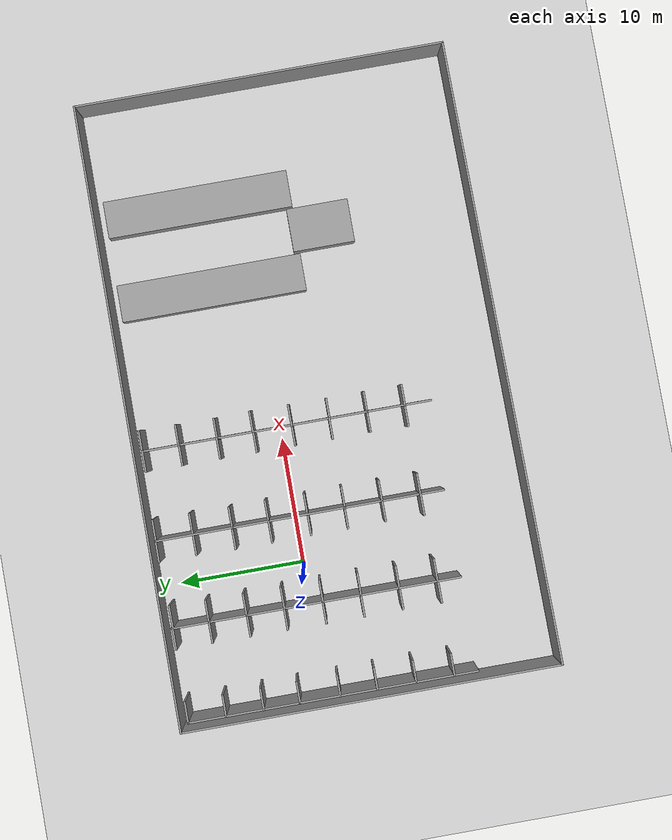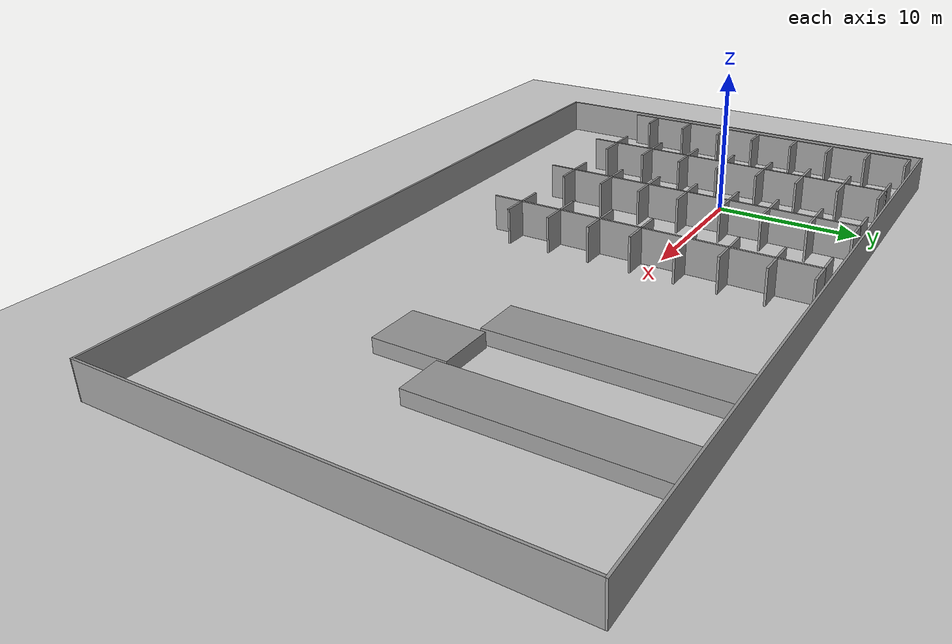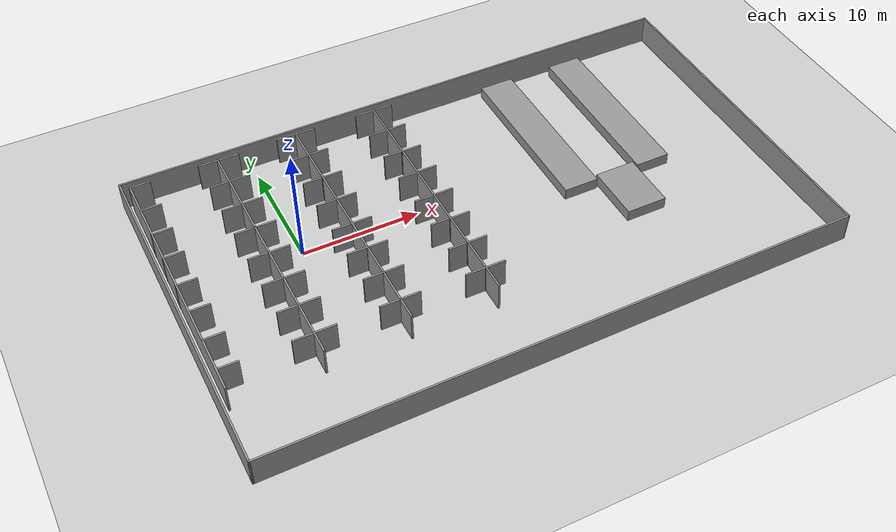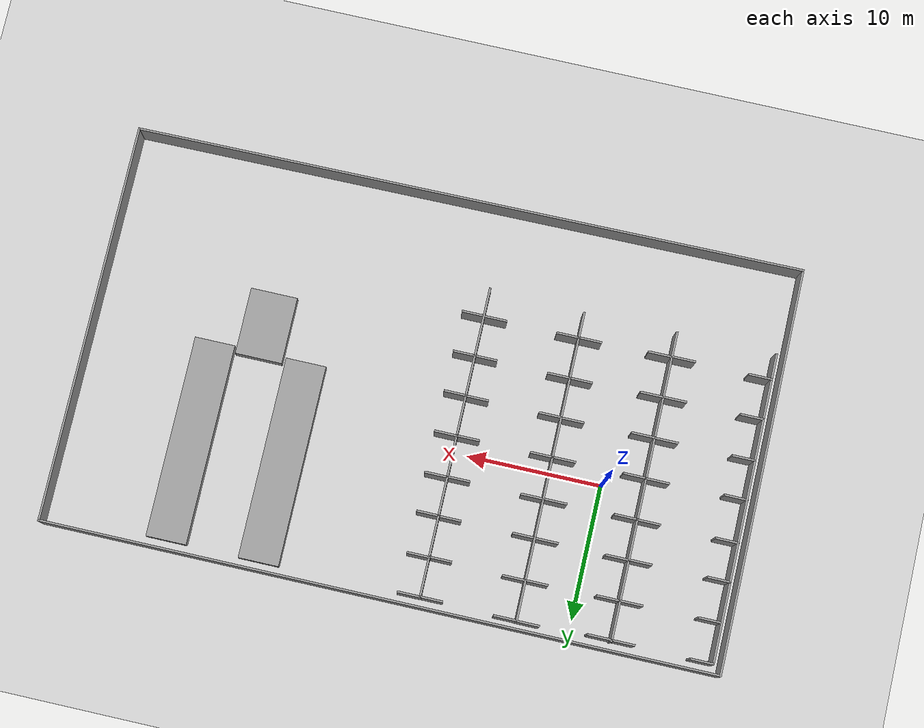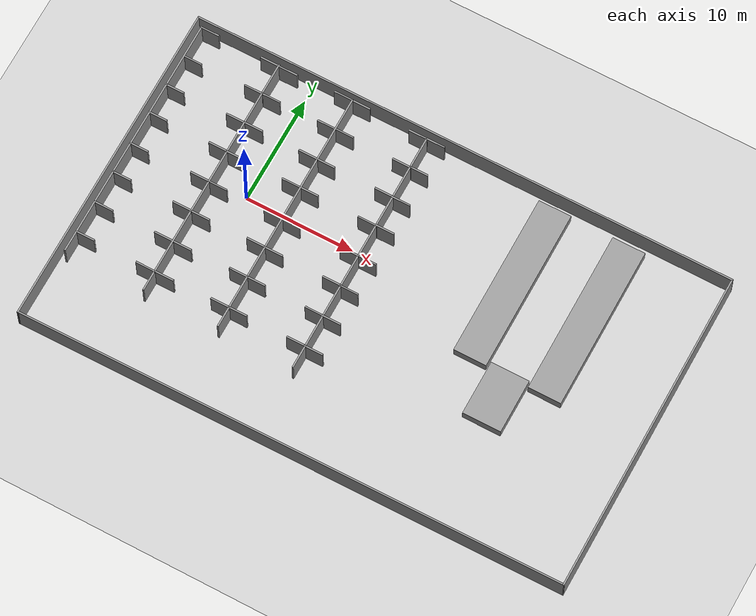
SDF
<sdf version="1.6">
 <world name="default">
  <light name="sun" type="directional">
   <pose>0 0 10 0 -0 0</pose>
   <diffuse>0.8 0.8 0.8 1</diffuse>
   <specular>0.2 0.2 0.2 1</specular>
   <attenuation>
    <range>1000</range>
    <constant>0.9</constant>
    <linear>0.01</linear>
    <quadratic>0.001</quadratic>
   </attenuation>
   <direction>-0.5 0.1 -0.9</direction>
   <spot><inner_angle>0</inner_angle><outer_angle>0</outer_angle><falloff>0</falloff></spot>
  </light>
  <model name="ground_plane">
   <static>1</static>
   <link name="link">
    <collision name="collision">
     <geometry><plane><normal>0 0 1</normal><size>100 100</size></plane></geometry>
     <surface>
      <contact><collide_bitmask>65535</collide_bitmask></contact>
      <friction><ode><mu>100</mu><mu2>50</mu2></ode></friction>
     </surface>
    </collision>
    <visual name="visual">
     <cast_shadows>0</cast_shadows>
     <geometry><plane><normal>0 0 1</normal><size>100 100</size></plane></geometry>
     <material>
      <script><uri>file://media/materials/scripts/gazebo.material</uri><name>Gazebo/Grey</name></script>
     </material>
    </visual>
   </link>
  </model>
  <gravity>0 0 -9.8</gravity>
  <magnetic_field>6e-06 2.3e-05 -4.2e-05</magnetic_field>
  <atmosphere type="adiabatic"/>
  <physics type="ode">
   <max_step_size>0.001</max_step_size>
   <real_time_factor>1</real_time_factor>
   <real_time_update_rate>1000</real_time_update_rate>
  </physics>
  <scene><ambient>0.4 0.4 0.4 1</ambient><background>0.7 0.7 0.7 1</background><shadows>1</shadows></scene>
  <spherical_coordinates>
   <surface_model>EARTH_WGS84</surface_model>
   <latitude_deg>0</latitude_deg>
   <longitude_deg>0</longitude_deg>
   <elevation>0</elevation>
   <heading_deg>0</heading_deg>
  </spherical_coordinates>
  <model name="Warehouse_Map">
   <link name="Wall_0">
    <pose>-0.000412 -14.8629 0 0 -0 0.007442</pose>
    <visual name="Wall_0_Visual">
     <pose>0 0 1.25 0 -0 0</pose>
     <geometry><box><size>50 0.15 2.5</size></box></geometry>
     <material>
      <script><uri>file://media/materials/scripts/gazebo.material</uri><name>Gazebo/Grey</name></script>
      <ambient>1 1 1 1</ambient>
      <shader type="pixel"/>
     </material>
     <meta><layer>0</layer></meta>
    </visual>
    <collision name="Wall_0_Collision">
     <pose>0 0 1.25 0 -0 0</pose>
     <geometry><box><size>50 0.15 2.5</size></box></geometry>
     <surface>
      <friction>
       <ode><mu>1</mu><mu2>1</mu2><fdir1>0 0 0</fdir1><slip1>0</slip1><slip2>0</slip2></ode>
       <torsional>
        <coefficient>1</coefficient>
        <patch_radius>0</patch_radius>
        <surface_radius>0</surface_radius>
        <use_patch_radius>1</use_patch_radius>
        <ode><slip>0</slip></ode>
       </torsional>
      </friction>
      <bounce><restitution_coefficient>0</restitution_coefficient><threshold>1e+06</threshold></bounce>
      <contact>
       <collide_without_contact>0</collide_without_contact>
       <collide_without_contact_bitmask>1</collide_without_contact_bitmask>
       <collide_bitmask>1</collide_bitmask>
       <ode>
        <soft_cfm>0</soft_cfm>
        <soft_erp>0.2</soft_erp>
        <kp>1e+13</kp>
        <kd>1</kd>
        <max_vel>0.01</max_vel>
        <min_depth>0</min_depth>
       </ode>
       <bullet>
        <split_impulse>1</split_impulse>
        <split_impulse_penetration_threshold>-0.01</split_impulse_penetration_threshold>
        <soft_cfm>0</soft_cfm>
        <soft_erp>0.2</soft_erp>
        <kp>1e+13</kp>
        <kd>1</kd>
       </bullet>
      </contact>
     </surface>
    </collision>
   </link>
   <link name="Wall_10">
    <pose>-23.4629 14.3501 0 0 -0 3.14159</pose>
    <visual name="Wall_10_Visual">
     <pose>0 0 1.25 0 -0 0</pose>
     <geometry><box><size>1.75 0.15 2.5</size></box></geometry>
     <material>
      <script><uri>file://media/materials/scripts/gazebo.material</uri><name>Gazebo/Grey</name></script>
      <ambient>1 1 1 1</ambient>
      <shader type="pixel"/>
     </material>
     <meta><layer>0</layer></meta>
    </visual>
    <collision name="Wall_10_Collision">
     <pose>0 0 1.25 0 -0 0</pose>
     <geometry><box><size>1.75 0.15 2.5</size></box></geometry>
     <surface>
      <friction>
       <ode><mu>1</mu><mu2>1</mu2><fdir1>0 0 0</fdir1><slip1>0</slip1><slip2>0</slip2></ode>
       <torsional>
        <coefficient>1</coefficient>
        <patch_radius>0</patch_radius>
        <surface_radius>0</surface_radius>
        <use_patch_radius>1</use_patch_radius>
        <ode><slip>0</slip></ode>
       </torsional>
      </friction>
      <bounce><restitution_coefficient>0</restitution_coefficient><threshold>1e+06</threshold></bounce>
      <contact>
       <collide_without_contact>0</collide_without_contact>
       <collide_without_contact_bitmask>1</collide_without_contact_bitmask>
       <collide_bitmask>1</collide_bitmask>
       <ode>
        <soft_cfm>0</soft_cfm>
        <soft_erp>0.2</soft_erp>
        <kp>1e+13</kp>
        <kd>1</kd>
        <max_vel>0.01</max_vel>
        <min_depth>0</min_depth>
       </ode>
       <bullet>
        <split_impulse>1</split_impulse>
        <split_impulse_penetration_threshold>-0.01</split_impulse_penetration_threshold>
        <soft_cfm>0</soft_cfm>
        <soft_erp>0.2</soft_erp>
        <kp>1e+13</kp>
        <kd>1</kd>
       </bullet>
      </contact>
     </surface>
    </collision>
   </link>
   <link name="Wall_10_clone">
    <pose>-23.4598 11.3691 0 0 -0 3.14159</pose>
    <visual name="Wall_10_Visual">
     <pose>0 0 1.25 0 -0 0</pose>
     <geometry><box><size>1.75 0.15 2.5</size></box></geometry>
     <material>
      <script><uri>file://media/materials/scripts/gazebo.material</uri><name>Gazebo/Grey</name></script>
      <ambient>1 1 1 1</ambient>
      <shader type="pixel"/>
     </material>
     <meta><layer>0</layer></meta>
    </visual>
    <collision name="Wall_10_Collision">
     <pose>0 0 1.25 0 -0 0</pose>
     <geometry><box><size>1.75 0.15 2.5</size></box></geometry>
     <surface>
      <friction>
       <ode><mu>1</mu><mu2>1</mu2><fdir1>0 0 0</fdir1><slip1>0</slip1><slip2>0</slip2></ode>
       <torsional>
        <coefficient>1</coefficient>
        <patch_radius>0</patch_radius>
        <surface_radius>0</surface_radius>
        <use_patch_radius>1</use_patch_radius>
        <ode><slip>0</slip></ode>
       </torsional>
      </friction>
      <bounce><restitution_coefficient>0</restitution_coefficient><threshold>1e+06</threshold></bounce>
      <contact>
       <collide_without_contact>0</collide_without_contact>
       <collide_without_contact_bitmask>1</collide_without_contact_bitmask>
       <collide_bitmask>1</collide_bitmask>
       <ode>
        <soft_cfm>0</soft_cfm>
        <soft_erp>0.2</soft_erp>
        <kp>1e+13</kp>
        <kd>1</kd>
        <max_vel>0.01</max_vel>
        <min_depth>0</min_depth>
       </ode>
       <bullet>
        <split_impulse>1</split_impulse>
        <split_impulse_penetration_threshold>-0.01</split_impulse_penetration_threshold>
        <soft_cfm>0</soft_cfm>
        <soft_erp>0.2</soft_erp>
        <kp>1e+13</kp>
        <kd>1</kd>
       </bullet>
      </contact>
     </surface>
    </collision>
   </link>
   <link name="Wall_10_clone_0">
    <pose>-23.4859 8.40001 0 0 -0 3.14159</pose>
    <visual name="Wall_10_Visual">
     <pose>0 0 1.25 0 -0 0</pose>
     <geometry><box><size>1.75 0.15 2.5</size></box></geometry>
     <material>
      <script><uri>file://media/materials/scripts/gazebo.material</uri><name>Gazebo/Grey</name></script>
      <ambient>1 1 1 1</ambient>
      <shader type="pixel"/>
     </material>
     <meta><layer>0</layer></meta>
    </visual>
    <collision name="Wall_10_Collision">
     <pose>0 0 1.25 0 -0 0</pose>
     <geometry><box><size>1.75 0.15 2.5</size></box></geometry>
     <surface>
      <friction>
       <ode><mu>1</mu><mu2>1</mu2><fdir1>0 0 0</fdir1><slip1>0</slip1><slip2>0</slip2></ode>
       <torsional>
        <coefficient>1</coefficient>
        <patch_radius>0</patch_radius>
        <surface_radius>0</surface_radius>
        <use_patch_radius>1</use_patch_radius>
        <ode><slip>0</slip></ode>
       </torsional>
      </friction>
      <bounce><restitution_coefficient>0</restitution_coefficient><threshold>1e+06</threshold></bounce>
      <contact>
       <collide_without_contact>0</collide_without_contact>
       <collide_without_contact_bitmask>1</collide_without_contact_bitmask>
       <collide_bitmask>1</collide_bitmask>
       <ode>
        <soft_cfm>0</soft_cfm>
        <soft_erp>0.2</soft_erp>
        <kp>1e+13</kp>
        <kd>1</kd>
        <max_vel>0.01</max_vel>
        <min_depth>0</min_depth>
       </ode>
       <bullet>
        <split_impulse>1</split_impulse>
        <split_impulse_penetration_threshold>-0.01</split_impulse_penetration_threshold>
        <soft_cfm>0</soft_cfm>
        <soft_erp>0.2</soft_erp>
        <kp>1e+13</kp>
        <kd>1</kd>
       </bullet>
      </contact>
     </surface>
    </collision>
   </link>
   <link name="Wall_10_clone_1">
    <pose>-23.4859 5.53501 0 0 -0 3.14159</pose>
    <visual name="Wall_10_Visual">
     <pose>0 0 1.25 0 -0 0</pose>
     <geometry><box><size>1.75 0.15 2.5</size></box></geometry>
     <material>
      <script><uri>file://media/materials/scripts/gazebo.material</uri><name>Gazebo/Grey</name></script>
      <ambient>1 1 1 1</ambient>
      <shader type="pixel"/>
     </material>
     <meta><layer>0</layer></meta>
    </visual>
    <collision name="Wall_10_Collision">
     <pose>0 0 1.25 0 -0 0</pose>
     <geometry><box><size>1.75 0.15 2.5</size></box></geometry>
     <surface>
      <friction>
       <ode><mu>1</mu><mu2>1</mu2><fdir1>0 0 0</fdir1><slip1>0</slip1><slip2>0</slip2></ode>
       <torsional>
        <coefficient>1</coefficient>
        <patch_radius>0</patch_radius>
        <surface_radius>0</surface_radius>
        <use_patch_radius>1</use_patch_radius>
        <ode><slip>0</slip></ode>
       </torsional>
      </friction>
      <bounce><restitution_coefficient>0</restitution_coefficient><threshold>1e+06</threshold></bounce>
      <contact>
       <collide_without_contact>0</collide_without_contact>
       <collide_without_contact_bitmask>1</collide_without_contact_bitmask>
       <collide_bitmask>1</collide_bitmask>
       <ode>
        <soft_cfm>0</soft_cfm>
        <soft_erp>0.2</soft_erp>
        <kp>1e+13</kp>
        <kd>1</kd>
        <max_vel>0.01</max_vel>
        <min_depth>0</min_depth>
       </ode>
       <bullet>
        <split_impulse>1</split_impulse>
        <split_impulse_penetration_threshold>-0.01</split_impulse_penetration_threshold>
        <soft_cfm>0</soft_cfm>
        <soft_erp>0.2</soft_erp>
        <kp>1e+13</kp>
        <kd>1</kd>
       </bullet>
      </contact>
     </surface>
    </collision>
   </link>
   <link name="Wall_10_clone_10">
    <pose>-17.7362 5.4991 0 0 -0 3.14159</pose>
    <visual name="Wall_10_Visual">
     <pose>0 0 1.25 0 -0 0</pose>
     <geometry><box><size>1.75 0.15 2.5</size></box></geometry>
     <material>
      <script><uri>file://media/materials/scripts/gazebo.material</uri><name>Gazebo/Grey</name></script>
      <ambient>1 1 1 1</ambient>
      <shader type="pixel"/>
     </material>
     <meta><layer>0</layer></meta>
    </visual>
    <collision name="Wall_10_Collision">
     <pose>0 0 1.25 0 -0 0</pose>
     <geometry><box><size>1.75 0.15 2.5</size></box></geometry>
     <surface>
      <friction>
       <ode><mu>1</mu><mu2>1</mu2><fdir1>0 0 0</fdir1><slip1>0</slip1><slip2>0</slip2></ode>
       <torsional>
        <coefficient>1</coefficient>
        <patch_radius>0</patch_radius>
        <surface_radius>0</surface_radius>
        <use_patch_radius>1</use_patch_radius>
        <ode><slip>0</slip></ode>
       </torsional>
      </friction>
      <bounce><restitution_coefficient>0</restitution_coefficient><threshold>1e+06</threshold></bounce>
      <contact>
       <collide_without_contact>0</collide_without_contact>
       <collide_without_contact_bitmask>1</collide_without_contact_bitmask>
       <collide_bitmask>1</collide_bitmask>
       <ode>
        <soft_cfm>0</soft_cfm>
        <soft_erp>0.2</soft_erp>
        <kp>1e+13</kp>
        <kd>1</kd>
        <max_vel>0.01</max_vel>
        <min_depth>0</min_depth>
       </ode>
       <bullet>
        <split_impulse>1</split_impulse>
        <split_impulse_penetration_threshold>-0.01</split_impulse_penetration_threshold>
        <soft_cfm>0</soft_cfm>
        <soft_erp>0.2</soft_erp>
        <kp>1e+13</kp>
        <kd>1</kd>
       </bullet>
      </contact>
     </surface>
    </collision>
   </link>
   <link name="Wall_10_clone_11">
    <pose>-17.728 8.43865 0 0 -0 3.14159</pose>
    <visual name="Wall_10_Visual">
     <pose>0 0 1.25 0 -0 0</pose>
     <geometry><box><size>1.75 0.15 2.5</size></box></geometry>
     <material>
      <script><uri>file://media/materials/scripts/gazebo.material</uri><name>Gazebo/Grey</name></script>
      <ambient>1 1 1 1</ambient>
      <shader type="pixel"/>
     </material>
     <meta><layer>0</layer></meta>
    </visual>
    <collision name="Wall_10_Collision">
     <pose>0 0 1.25 0 -0 0</pose>
     <geometry><box><size>1.75 0.15 2.5</size></box></geometry>
     <surface>
      <friction>
       <ode><mu>1</mu><mu2>1</mu2><fdir1>0 0 0</fdir1><slip1>0</slip1><slip2>0</slip2></ode>
       <torsional>
        <coefficient>1</coefficient>
        <patch_radius>0</patch_radius>
        <surface_radius>0</surface_radius>
        <use_patch_radius>1</use_patch_radius>
        <ode><slip>0</slip></ode>
       </torsional>
      </friction>
      <bounce><restitution_coefficient>0</restitution_coefficient><threshold>1e+06</threshold></bounce>
      <contact>
       <collide_without_contact>0</collide_without_contact>
       <collide_without_contact_bitmask>1</collide_without_contact_bitmask>
       <collide_bitmask>1</collide_bitmask>
       <ode>
        <soft_cfm>0</soft_cfm>
        <soft_erp>0.2</soft_erp>
        <kp>1e+13</kp>
        <kd>1</kd>
        <max_vel>0.01</max_vel>
        <min_depth>0</min_depth>
       </ode>
       <bullet>
        <split_impulse>1</split_impulse>
        <split_impulse_penetration_threshold>-0.01</split_impulse_penetration_threshold>
        <soft_cfm>0</soft_cfm>
        <soft_erp>0.2</soft_erp>
        <kp>1e+13</kp>
        <kd>1</kd>
       </bullet>
      </contact>
     </surface>
    </collision>
   </link>
   <link name="Wall_10_clone_12">
    <pose>-17.6835 11.4373 0 0 -0 3.14159</pose>
    <visual name="Wall_10_Visual">
     <pose>0 0 1.25 0 -0 0</pose>
     <geometry><box><size>1.75 0.15 2.5</size></box></geometry>
     <material>
      <script><uri>file://media/materials/scripts/gazebo.material</uri><name>Gazebo/Grey</name></script>
      <ambient>1 1 1 1</ambient>
      <shader type="pixel"/>
     </material>
     <meta><layer>0</layer></meta>
    </visual>
    <collision name="Wall_10_Collision">
     <pose>0 0 1.25 0 -0 0</pose>
     <geometry><box><size>1.75 0.15 2.5</size></box></geometry>
     <surface>
      <friction>
       <ode><mu>1</mu><mu2>1</mu2><fdir1>0 0 0</fdir1><slip1>0</slip1><slip2>0</slip2></ode>
       <torsional>
        <coefficient>1</coefficient>
        <patch_radius>0</patch_radius>
        <surface_radius>0</surface_radius>
        <use_patch_radius>1</use_patch_radius>
        <ode><slip>0</slip></ode>
       </torsional>
      </friction>
      <bounce><restitution_coefficient>0</restitution_coefficient><threshold>1e+06</threshold></bounce>
      <contact>
       <collide_without_contact>0</collide_without_contact>
       <collide_without_contact_bitmask>1</collide_without_contact_bitmask>
       <collide_bitmask>1</collide_bitmask>
       <ode>
        <soft_cfm>0</soft_cfm>
        <soft_erp>0.2</soft_erp>
        <kp>1e+13</kp>
        <kd>1</kd>
        <max_vel>0.01</max_vel>
        <min_depth>0</min_depth>
       </ode>
       <bullet>
        <split_impulse>1</split_impulse>
        <split_impulse_penetration_threshold>-0.01</split_impulse_penetration_threshold>
        <soft_cfm>0</soft_cfm>
        <soft_erp>0.2</soft_erp>
        <kp>1e+13</kp>
        <kd>1</kd>
       </bullet>
      </contact>
     </surface>
    </collision>
   </link>
   <link name="Wall_10_clone_13">
    <pose>-17.7158 14.3021 0 0 -0 3.14159</pose>
    <visual name="Wall_10_Visual">
     <pose>0 0 1.25 0 -0 0</pose>
     <geometry><box><size>1.75 0.15 2.5</size></box></geometry>
     <material>
      <script><uri>file://media/materials/scripts/gazebo.material</uri><name>Gazebo/Grey</name></script>
      <ambient>1 1 1 1</ambient>
      <shader type="pixel"/>
     </material>
     <meta><layer>0</layer></meta>
    </visual>
    <collision name="Wall_10_Collision">
     <pose>0 0 1.25 0 -0 0</pose>
     <geometry><box><size>1.75 0.15 2.5</size></box></geometry>
     <surface>
      <friction>
       <ode><mu>1</mu><mu2>1</mu2><fdir1>0 0 0</fdir1><slip1>0</slip1><slip2>0</slip2></ode>
       <torsional>
        <coefficient>1</coefficient>
        <patch_radius>0</patch_radius>
        <surface_radius>0</surface_radius>
        <use_patch_radius>1</use_patch_radius>
        <ode><slip>0</slip></ode>
       </torsional>
      </friction>
      <bounce><restitution_coefficient>0</restitution_coefficient><threshold>1e+06</threshold></bounce>
      <contact>
       <collide_without_contact>0</collide_without_contact>
       <collide_without_contact_bitmask>1</collide_without_contact_bitmask>
       <collide_bitmask>1</collide_bitmask>
       <ode>
        <soft_cfm>0</soft_cfm>
        <soft_erp>0.2</soft_erp>
        <kp>1e+13</kp>
        <kd>1</kd>
        <max_vel>0.01</max_vel>
        <min_depth>0</min_depth>
       </ode>
       <bullet>
        <split_impulse>1</split_impulse>
        <split_impulse_penetration_threshold>-0.01</split_impulse_penetration_threshold>
        <soft_cfm>0</soft_cfm>
        <soft_erp>0.2</soft_erp>
        <kp>1e+13</kp>
        <kd>1</kd>
       </bullet>
      </contact>
     </surface>
    </collision>
   </link>
   <link name="Wall_10_clone_14">
    <pose>-15.9666 14.2849 0 0 -0 3.14159</pose>
    <visual name="Wall_10_Visual">
     <pose>0 0 1.25 0 -0 0</pose>
     <geometry><box><size>1.75 0.15 2.5</size></box></geometry>
     <material>
      <script><uri>file://media/materials/scripts/gazebo.material</uri><name>Gazebo/Grey</name></script>
      <ambient>1 1 1 1</ambient>
      <shader type="pixel"/>
     </material>
     <meta><layer>0</layer></meta>
    </visual>
    <collision name="Wall_10_Collision">
     <pose>0 0 1.25 0 -0 0</pose>
     <geometry><box><size>1.75 0.15 2.5</size></box></geometry>
     <surface>
      <friction>
       <ode><mu>1</mu><mu2>1</mu2><fdir1>0 0 0</fdir1><slip1>0</slip1><slip2>0</slip2></ode>
       <torsional>
        <coefficient>1</coefficient>
        <patch_radius>0</patch_radius>
        <surface_radius>0</surface_radius>
        <use_patch_radius>1</use_patch_radius>
        <ode><slip>0</slip></ode>
       </torsional>
      </friction>
      <bounce><restitution_coefficient>0</restitution_coefficient><threshold>1e+06</threshold></bounce>
      <contact>
       <collide_without_contact>0</collide_without_contact>
       <collide_without_contact_bitmask>1</collide_without_contact_bitmask>
       <collide_bitmask>1</collide_bitmask>
       <ode>
        <soft_cfm>0</soft_cfm>
        <soft_erp>0.2</soft_erp>
        <kp>1e+13</kp>
        <kd>1</kd>
        <max_vel>0.01</max_vel>
        <min_depth>0</min_depth>
       </ode>
       <bullet>
        <split_impulse>1</split_impulse>
        <split_impulse_penetration_threshold>-0.01</split_impulse_penetration_threshold>
        <soft_cfm>0</soft_cfm>
        <soft_erp>0.2</soft_erp>
        <kp>1e+13</kp>
        <kd>1</kd>
       </bullet>
      </contact>
     </surface>
    </collision>
   </link>
   <link name="Wall_10_clone_15">
    <pose>-16.0611 11.447 0 0 -0 3.14159</pose>
    <visual name="Wall_10_Visual">
     <pose>0 0 1.25 0 -0 0</pose>
     <geometry><box><size>1.75 0.15 2.5</size></box></geometry>
     <material>
      <script><uri>file://media/materials/scripts/gazebo.material</uri><name>Gazebo/Grey</name></script>
      <ambient>1 1 1 1</ambient>
      <shader type="pixel"/>
     </material>
     <meta><layer>0</layer></meta>
    </visual>
    <collision name="Wall_10_Collision">
     <pose>0 0 1.25 0 -0 0</pose>
     <geometry><box><size>1.75 0.15 2.5</size></box></geometry>
     <surface>
      <friction>
       <ode><mu>1</mu><mu2>1</mu2><fdir1>0 0 0</fdir1><slip1>0</slip1><slip2>0</slip2></ode>
       <torsional>
        <coefficient>1</coefficient>
        <patch_radius>0</patch_radius>
        <surface_radius>0</surface_radius>
        <use_patch_radius>1</use_patch_radius>
        <ode><slip>0</slip></ode>
       </torsional>
      </friction>
      <bounce><restitution_coefficient>0</restitution_coefficient><threshold>1e+06</threshold></bounce>
      <contact>
       <collide_without_contact>0</collide_without_contact>
       <collide_without_contact_bitmask>1</collide_without_contact_bitmask>
       <collide_bitmask>1</collide_bitmask>
       <ode>
        <soft_cfm>0</soft_cfm>
        <soft_erp>0.2</soft_erp>
        <kp>1e+13</kp>
        <kd>1</kd>
        <max_vel>0.01</max_vel>
        <min_depth>0</min_depth>
       </ode>
       <bullet>
        <split_impulse>1</split_impulse>
        <split_impulse_penetration_threshold>-0.01</split_impulse_penetration_threshold>
        <soft_cfm>0</soft_cfm>
        <soft_erp>0.2</soft_erp>
        <kp>1e+13</kp>
        <kd>1</kd>
       </bullet>
      </contact>
     </surface>
    </collision>
   </link>
   <link name="Wall_10_clone_16">
    <pose>-16.0702 8.46392 0 0 -0 3.14159</pose>
    <visual name="Wall_10_Visual">
     <pose>0 0 1.25 0 -0 0</pose>
     <geometry><box><size>1.75 0.15 2.5</size></box></geometry>
     <material>
      <script><uri>file://media/materials/scripts/gazebo.material</uri><name>Gazebo/Grey</name></script>
      <ambient>1 1 1 1</ambient>
      <shader type="pixel"/>
     </material>
     <meta><layer>0</layer></meta>
    </visual>
    <collision name="Wall_10_Collision">
     <pose>0 0 1.25 0 -0 0</pose>
     <geometry><box><size>1.75 0.15 2.5</size></box></geometry>
     <surface>
      <friction>
       <ode><mu>1</mu><mu2>1</mu2><fdir1>0 0 0</fdir1><slip1>0</slip1><slip2>0</slip2></ode>
       <torsional>
        <coefficient>1</coefficient>
        <patch_radius>0</patch_radius>
        <surface_radius>0</surface_radius>
        <use_patch_radius>1</use_patch_radius>
        <ode><slip>0</slip></ode>
       </torsional>
      </friction>
      <bounce><restitution_coefficient>0</restitution_coefficient><threshold>1e+06</threshold></bounce>
      <contact>
       <collide_without_contact>0</collide_without_contact>
       <collide_without_contact_bitmask>1</collide_without_contact_bitmask>
       <collide_bitmask>1</collide_bitmask>
       <ode>
        <soft_cfm>0</soft_cfm>
        <soft_erp>0.2</soft_erp>
        <kp>1e+13</kp>
        <kd>1</kd>
        <max_vel>0.01</max_vel>
        <min_depth>0</min_depth>
       </ode>
       <bullet>
        <split_impulse>1</split_impulse>
        <split_impulse_penetration_threshold>-0.01</split_impulse_penetration_threshold>
        <soft_cfm>0</soft_cfm>
        <soft_erp>0.2</soft_erp>
        <kp>1e+13</kp>
        <kd>1</kd>
       </bullet>
      </contact>
     </surface>
    </collision>
   </link>
   <link name="Wall_10_clone_17">
    <pose>-16.0699 5.48035 0 0 -0 3.14159</pose>
    <visual name="Wall_10_Visual">
     <pose>0 0 1.25 0 -0 0</pose>
     <geometry><box><size>1.75 0.15 2.5</size></box></geometry>
     <material>
      <script><uri>file://media/materials/scripts/gazebo.material</uri><name>Gazebo/Grey</name></script>
      <ambient>1 1 1 1</ambient>
      <shader type="pixel"/>
     </material>
     <meta><layer>0</layer></meta>
    </visual>
    <collision name="Wall_10_Collision">
     <pose>0 0 1.25 0 -0 0</pose>
     <geometry><box><size>1.75 0.15 2.5</size></box></geometry>
     <surface>
      <friction>
       <ode><mu>1</mu><mu2>1</mu2><fdir1>0 0 0</fdir1><slip1>0</slip1><slip2>0</slip2></ode>
       <torsional>
        <coefficient>1</coefficient>
        <patch_radius>0</patch_radius>
        <surface_radius>0</surface_radius>
        <use_patch_radius>1</use_patch_radius>
        <ode><slip>0</slip></ode>
       </torsional>
      </friction>
      <bounce><restitution_coefficient>0</restitution_coefficient><threshold>1e+06</threshold></bounce>
      <contact>
       <collide_without_contact>0</collide_without_contact>
       <collide_without_contact_bitmask>1</collide_without_contact_bitmask>
       <collide_bitmask>1</collide_bitmask>
       <ode>
        <soft_cfm>0</soft_cfm>
        <soft_erp>0.2</soft_erp>
        <kp>1e+13</kp>
        <kd>1</kd>
        <max_vel>0.01</max_vel>
        <min_depth>0</min_depth>
       </ode>
       <bullet>
        <split_impulse>1</split_impulse>
        <split_impulse_penetration_threshold>-0.01</split_impulse_penetration_threshold>
        <soft_cfm>0</soft_cfm>
        <soft_erp>0.2</soft_erp>
        <kp>1e+13</kp>
        <kd>1</kd>
       </bullet>
      </contact>
     </surface>
    </collision>
   </link>
   <link name="Wall_10_clone_18">
    <pose>-16.0825 2.42965 0 0 -0 3.14159</pose>
    <visual name="Wall_10_Visual">
     <pose>0 0 1.25 0 -0 0</pose>
     <geometry><box><size>1.75 0.15 2.5</size></box></geometry>
     <material>
      <script><uri>file://media/materials/scripts/gazebo.material</uri><name>Gazebo/Grey</name></script>
      <ambient>1 1 1 1</ambient>
      <shader type="pixel"/>
     </material>
     <meta><layer>0</layer></meta>
    </visual>
    <collision name="Wall_10_Collision">
     <pose>0 0 1.25 0 -0 0</pose>
     <geometry><box><size>1.75 0.15 2.5</size></box></geometry>
     <surface>
      <friction>
       <ode><mu>1</mu><mu2>1</mu2><fdir1>0 0 0</fdir1><slip1>0</slip1><slip2>0</slip2></ode>
       <torsional>
        <coefficient>1</coefficient>
        <patch_radius>0</patch_radius>
        <surface_radius>0</surface_radius>
        <use_patch_radius>1</use_patch_radius>
        <ode><slip>0</slip></ode>
       </torsional>
      </friction>
      <bounce><restitution_coefficient>0</restitution_coefficient><threshold>1e+06</threshold></bounce>
      <contact>
       <collide_without_contact>0</collide_without_contact>
       <collide_without_contact_bitmask>1</collide_without_contact_bitmask>
       <collide_bitmask>1</collide_bitmask>
       <ode>
        <soft_cfm>0</soft_cfm>
        <soft_erp>0.2</soft_erp>
        <kp>1e+13</kp>
        <kd>1</kd>
        <max_vel>0.01</max_vel>
        <min_depth>0</min_depth>
       </ode>
       <bullet>
        <split_impulse>1</split_impulse>
        <split_impulse_penetration_threshold>-0.01</split_impulse_penetration_threshold>
        <soft_cfm>0</soft_cfm>
        <soft_erp>0.2</soft_erp>
        <kp>1e+13</kp>
        <kd>1</kd>
       </bullet>
      </contact>
     </surface>
    </collision>
   </link>
   <link name="Wall_10_clone_19">
    <pose>-16.0514 -0.584713 0 0 -0 3.14159</pose>
    <visual name="Wall_10_Visual">
     <pose>0 0 1.25 0 -0 0</pose>
     <geometry><box><size>1.75 0.15 2.5</size></box></geometry>
     <material>
      <script><uri>file://media/materials/scripts/gazebo.material</uri><name>Gazebo/Grey</name></script>
      <ambient>1 1 1 1</ambient>
      <shader type="pixel"/>
     </material>
     <meta><layer>0</layer></meta>
    </visual>
    <collision name="Wall_10_Collision">
     <pose>0 0 1.25 0 -0 0</pose>
     <geometry><box><size>1.75 0.15 2.5</size></box></geometry>
     <surface>
      <friction>
       <ode><mu>1</mu><mu2>1</mu2><fdir1>0 0 0</fdir1><slip1>0</slip1><slip2>0</slip2></ode>
       <torsional>
        <coefficient>1</coefficient>
        <patch_radius>0</patch_radius>
        <surface_radius>0</surface_radius>
        <use_patch_radius>1</use_patch_radius>
        <ode><slip>0</slip></ode>
       </torsional>
      </friction>
      <bounce><restitution_coefficient>0</restitution_coefficient><threshold>1e+06</threshold></bounce>
      <contact>
       <collide_without_contact>0</collide_without_contact>
       <collide_without_contact_bitmask>1</collide_without_contact_bitmask>
       <collide_bitmask>1</collide_bitmask>
       <ode>
        <soft_cfm>0</soft_cfm>
        <soft_erp>0.2</soft_erp>
        <kp>1e+13</kp>
        <kd>1</kd>
        <max_vel>0.01</max_vel>
        <min_depth>0</min_depth>
       </ode>
       <bullet>
        <split_impulse>1</split_impulse>
        <split_impulse_penetration_threshold>-0.01</split_impulse_penetration_threshold>
        <soft_cfm>0</soft_cfm>
        <soft_erp>0.2</soft_erp>
        <kp>1e+13</kp>
        <kd>1</kd>
       </bullet>
      </contact>
     </surface>
    </collision>
   </link>
   <link name="Wall_10_clone_2">
    <pose>-23.4859 2.35766 0 0 -0 3.14159</pose>
    <visual name="Wall_10_Visual">
     <pose>0 0 1.25 0 -0 0</pose>
     <geometry><box><size>1.75 0.15 2.5</size></box></geometry>
     <material>
      <script><uri>file://media/materials/scripts/gazebo.material</uri><name>Gazebo/Grey</name></script>
      <ambient>1 1 1 1</ambient>
      <shader type="pixel"/>
     </material>
     <meta><layer>0</layer></meta>
    </visual>
    <collision name="Wall_10_Collision">
     <pose>0 0 1.25 0 -0 0</pose>
     <geometry><box><size>1.75 0.15 2.5</size></box></geometry>
     <surface>
      <friction>
       <ode><mu>1</mu><mu2>1</mu2><fdir1>0 0 0</fdir1><slip1>0</slip1><slip2>0</slip2></ode>
       <torsional>
        <coefficient>1</coefficient>
        <patch_radius>0</patch_radius>
        <surface_radius>0</surface_radius>
        <use_patch_radius>1</use_patch_radius>
        <ode><slip>0</slip></ode>
       </torsional>
      </friction>
      <bounce><restitution_coefficient>0</restitution_coefficient><threshold>1e+06</threshold></bounce>
      <contact>
       <collide_without_contact>0</collide_without_contact>
       <collide_without_contact_bitmask>1</collide_without_contact_bitmask>
       <collide_bitmask>1</collide_bitmask>
       <ode>
        <soft_cfm>0</soft_cfm>
        <soft_erp>0.2</soft_erp>
        <kp>1e+13</kp>
        <kd>1</kd>
        <max_vel>0.01</max_vel>
        <min_depth>0</min_depth>
       </ode>
       <bullet>
        <split_impulse>1</split_impulse>
        <split_impulse_penetration_threshold>-0.01</split_impulse_penetration_threshold>
        <soft_cfm>0</soft_cfm>
        <soft_erp>0.2</soft_erp>
        <kp>1e+13</kp>
        <kd>1</kd>
       </bullet>
      </contact>
     </surface>
    </collision>
   </link>
   <link name="Wall_10_clone_20">
    <pose>-16.0486 -3.62068 0 0 -0 3.14159</pose>
    <visual name="Wall_10_Visual">
     <pose>0 0 1.25 0 -0 0</pose>
     <geometry><box><size>1.75 0.15 2.5</size></box></geometry>
     <material>
      <script><uri>file://media/materials/scripts/gazebo.material</uri><name>Gazebo/Grey</name></script>
      <ambient>1 1 1 1</ambient>
      <shader type="pixel"/>
     </material>
     <meta><layer>0</layer></meta>
    </visual>
    <collision name="Wall_10_Collision">
     <pose>0 0 1.25 0 -0 0</pose>
     <geometry><box><size>1.75 0.15 2.5</size></box></geometry>
     <surface>
      <friction>
       <ode><mu>1</mu><mu2>1</mu2><fdir1>0 0 0</fdir1><slip1>0</slip1><slip2>0</slip2></ode>
       <torsional>
        <coefficient>1</coefficient>
        <patch_radius>0</patch_radius>
        <surface_radius>0</surface_radius>
        <use_patch_radius>1</use_patch_radius>
        <ode><slip>0</slip></ode>
       </torsional>
      </friction>
      <bounce><restitution_coefficient>0</restitution_coefficient><threshold>1e+06</threshold></bounce>
      <contact>
       <collide_without_contact>0</collide_without_contact>
       <collide_without_contact_bitmask>1</collide_without_contact_bitmask>
       <collide_bitmask>1</collide_bitmask>
       <ode>
        <soft_cfm>0</soft_cfm>
        <soft_erp>0.2</soft_erp>
        <kp>1e+13</kp>
        <kd>1</kd>
        <max_vel>0.01</max_vel>
        <min_depth>0</min_depth>
       </ode>
       <bullet>
        <split_impulse>1</split_impulse>
        <split_impulse_penetration_threshold>-0.01</split_impulse_penetration_threshold>
        <soft_cfm>0</soft_cfm>
        <soft_erp>0.2</soft_erp>
        <kp>1e+13</kp>
        <kd>1</kd>
       </bullet>
      </contact>
     </surface>
    </collision>
   </link>
   <link name="Wall_10_clone_21">
    <pose>-16.0078 -6.65175 0 0 -0 3.14159</pose>
    <visual name="Wall_10_Visual">
     <pose>0 0 1.25 0 -0 0</pose>
     <geometry><box><size>1.75 0.15 2.5</size></box></geometry>
     <material>
      <script><uri>file://media/materials/scripts/gazebo.material</uri><name>Gazebo/Grey</name></script>
      <ambient>1 1 1 1</ambient>
      <shader type="pixel"/>
     </material>
     <meta><layer>0</layer></meta>
    </visual>
    <collision name="Wall_10_Collision">
     <pose>0 0 1.25 0 -0 0</pose>
     <geometry><box><size>1.75 0.15 2.5</size></box></geometry>
     <surface>
      <friction>
       <ode><mu>1</mu><mu2>1</mu2><fdir1>0 0 0</fdir1><slip1>0</slip1><slip2>0</slip2></ode>
       <torsional>
        <coefficient>1</coefficient>
        <patch_radius>0</patch_radius>
        <surface_radius>0</surface_radius>
        <use_patch_radius>1</use_patch_radius>
        <ode><slip>0</slip></ode>
       </torsional>
      </friction>
      <bounce><restitution_coefficient>0</restitution_coefficient><threshold>1e+06</threshold></bounce>
      <contact>
       <collide_without_contact>0</collide_without_contact>
       <collide_without_contact_bitmask>1</collide_without_contact_bitmask>
       <collide_bitmask>1</collide_bitmask>
       <ode>
        <soft_cfm>0</soft_cfm>
        <soft_erp>0.2</soft_erp>
        <kp>1e+13</kp>
        <kd>1</kd>
        <max_vel>0.01</max_vel>
        <min_depth>0</min_depth>
       </ode>
       <bullet>
        <split_impulse>1</split_impulse>
        <split_impulse_penetration_threshold>-0.01</split_impulse_penetration_threshold>
        <soft_cfm>0</soft_cfm>
        <soft_erp>0.2</soft_erp>
        <kp>1e+13</kp>
        <kd>1</kd>
       </bullet>
      </contact>
     </surface>
    </collision>
   </link>
   <link name="Wall_10_clone_21_clone">
    <pose>-10.8177 14.4759 0 0 -0 3.14159</pose>
    <visual name="Wall_10_Visual">
     <pose>0 0 1.25 0 -0 0</pose>
     <geometry><box><size>1.75 0.15 2.5</size></box></geometry>
     <material>
      <script><uri>file://media/materials/scripts/gazebo.material</uri><name>Gazebo/Grey</name></script>
      <ambient>1 1 1 1</ambient>
      <shader type="pixel"/>
     </material>
     <meta><layer>0</layer></meta>
    </visual>
    <collision name="Wall_10_Collision">
     <pose>0 0 1.25 0 -0 0</pose>
     <geometry><box><size>1.75 0.15 2.5</size></box></geometry>
     <surface>
      <friction>
       <ode><mu>1</mu><mu2>1</mu2><fdir1>0 0 0</fdir1><slip1>0</slip1><slip2>0</slip2></ode>
       <torsional>
        <coefficient>1</coefficient>
        <patch_radius>0</patch_radius>
        <surface_radius>0</surface_radius>
        <use_patch_radius>1</use_patch_radius>
        <ode><slip>0</slip></ode>
       </torsional>
      </friction>
      <bounce><restitution_coefficient>0</restitution_coefficient><threshold>1e+06</threshold></bounce>
      <contact>
       <collide_without_contact>0</collide_without_contact>
       <collide_without_contact_bitmask>1</collide_without_contact_bitmask>
       <collide_bitmask>1</collide_bitmask>
       <ode>
        <soft_cfm>0</soft_cfm>
        <soft_erp>0.2</soft_erp>
        <kp>1e+13</kp>
        <kd>1</kd>
        <max_vel>0.01</max_vel>
        <min_depth>0</min_depth>
       </ode>
       <bullet>
        <split_impulse>1</split_impulse>
        <split_impulse_penetration_threshold>-0.01</split_impulse_penetration_threshold>
        <soft_cfm>0</soft_cfm>
        <soft_erp>0.2</soft_erp>
        <kp>1e+13</kp>
        <kd>1</kd>
       </bullet>
      </contact>
     </surface>
    </collision>
   </link>
   <link name="Wall_10_clone_21_clone_0">
    <pose>-9.18611 14.4524 0 0 -0 3.14159</pose>
    <visual name="Wall_10_Visual">
     <pose>0 0 1.25 0 -0 0</pose>
     <geometry><box><size>1.75 0.15 2.5</size></box></geometry>
     <material>
      <script><uri>file://media/materials/scripts/gazebo.material</uri><name>Gazebo/Grey</name></script>
      <ambient>1 1 1 1</ambient>
      <shader type="pixel"/>
     </material>
     <meta><layer>0</layer></meta>
    </visual>
    <collision name="Wall_10_Collision">
     <pose>0 0 1.25 0 -0 0</pose>
     <geometry><box><size>1.75 0.15 2.5</size></box></geometry>
     <surface>
      <friction>
       <ode><mu>1</mu><mu2>1</mu2><fdir1>0 0 0</fdir1><slip1>0</slip1><slip2>0</slip2></ode>
       <torsional>
        <coefficient>1</coefficient>
        <patch_radius>0</patch_radius>
        <surface_radius>0</surface_radius>
        <use_patch_radius>1</use_patch_radius>
        <ode><slip>0</slip></ode>
       </torsional>
      </friction>
      <bounce><restitution_coefficient>0</restitution_coefficient><threshold>1e+06</threshold></bounce>
      <contact>
       <collide_without_contact>0</collide_without_contact>
       <collide_without_contact_bitmask>1</collide_without_contact_bitmask>
       <collide_bitmask>1</collide_bitmask>
       <ode>
        <soft_cfm>0</soft_cfm>
        <soft_erp>0.2</soft_erp>
        <kp>1e+13</kp>
        <kd>1</kd>
        <max_vel>0.01</max_vel>
        <min_depth>0</min_depth>
       </ode>
       <bullet>
        <split_impulse>1</split_impulse>
        <split_impulse_penetration_threshold>-0.01</split_impulse_penetration_threshold>
        <soft_cfm>0</soft_cfm>
        <soft_erp>0.2</soft_erp>
        <kp>1e+13</kp>
        <kd>1</kd>
       </bullet>
      </contact>
     </surface>
    </collision>
   </link>
   <link name="Wall_10_clone_21_clone_1">
    <pose>-10.8033 11.5118 0 0 -0 3.14159</pose>
    <visual name="Wall_10_Visual">
     <pose>0 0 1.25 0 -0 0</pose>
     <geometry><box><size>1.75 0.15 2.5</size></box></geometry>
     <material>
      <script><uri>file://media/materials/scripts/gazebo.material</uri><name>Gazebo/Grey</name></script>
      <ambient>1 1 1 1</ambient>
      <shader type="pixel"/>
     </material>
     <meta><layer>0</layer></meta>
    </visual>
    <collision name="Wall_10_Collision">
     <pose>0 0 1.25 0 -0 0</pose>
     <geometry><box><size>1.75 0.15 2.5</size></box></geometry>
     <surface>
      <friction>
       <ode><mu>1</mu><mu2>1</mu2><fdir1>0 0 0</fdir1><slip1>0</slip1><slip2>0</slip2></ode>
       <torsional>
        <coefficient>1</coefficient>
        <patch_radius>0</patch_radius>
        <surface_radius>0</surface_radius>
        <use_patch_radius>1</use_patch_radius>
        <ode><slip>0</slip></ode>
       </torsional>
      </friction>
      <bounce><restitution_coefficient>0</restitution_coefficient><threshold>1e+06</threshold></bounce>
      <contact>
       <collide_without_contact>0</collide_without_contact>
       <collide_without_contact_bitmask>1</collide_without_contact_bitmask>
       <collide_bitmask>1</collide_bitmask>
       <ode>
        <soft_cfm>0</soft_cfm>
        <soft_erp>0.2</soft_erp>
        <kp>1e+13</kp>
        <kd>1</kd>
        <max_vel>0.01</max_vel>
        <min_depth>0</min_depth>
       </ode>
       <bullet>
        <split_impulse>1</split_impulse>
        <split_impulse_penetration_threshold>-0.01</split_impulse_penetration_threshold>
        <soft_cfm>0</soft_cfm>
        <soft_erp>0.2</soft_erp>
        <kp>1e+13</kp>
        <kd>1</kd>
       </bullet>
      </contact>
     </surface>
    </collision>
   </link>
   <link name="Wall_10_clone_21_clone_10">
    <pose>-9.22502 -0.53089 0 0 -0 3.14159</pose>
    <visual name="Wall_10_Visual">
     <pose>0 0 1.25 0 -0 0</pose>
     <geometry><box><size>1.75 0.15 2.5</size></box></geometry>
     <material>
      <script><uri>file://media/materials/scripts/gazebo.material</uri><name>Gazebo/Grey</name></script>
      <ambient>1 1 1 1</ambient>
      <shader type="pixel"/>
     </material>
     <meta><layer>0</layer></meta>
    </visual>
    <collision name="Wall_10_Collision">
     <pose>0 0 1.25 0 -0 0</pose>
     <geometry><box><size>1.75 0.15 2.5</size></box></geometry>
     <surface>
      <friction>
       <ode><mu>1</mu><mu2>1</mu2><fdir1>0 0 0</fdir1><slip1>0</slip1><slip2>0</slip2></ode>
       <torsional>
        <coefficient>1</coefficient>
        <patch_radius>0</patch_radius>
        <surface_radius>0</surface_radius>
        <use_patch_radius>1</use_patch_radius>
        <ode><slip>0</slip></ode>
       </torsional>
      </friction>
      <bounce><restitution_coefficient>0</restitution_coefficient><threshold>1e+06</threshold></bounce>
      <contact>
       <collide_without_contact>0</collide_without_contact>
       <collide_without_contact_bitmask>1</collide_without_contact_bitmask>
       <collide_bitmask>1</collide_bitmask>
       <ode>
        <soft_cfm>0</soft_cfm>
        <soft_erp>0.2</soft_erp>
        <kp>1e+13</kp>
        <kd>1</kd>
        <max_vel>0.01</max_vel>
        <min_depth>0</min_depth>
       </ode>
       <bullet>
        <split_impulse>1</split_impulse>
        <split_impulse_penetration_threshold>-0.01</split_impulse_penetration_threshold>
        <soft_cfm>0</soft_cfm>
        <soft_erp>0.2</soft_erp>
        <kp>1e+13</kp>
        <kd>1</kd>
       </bullet>
      </contact>
     </surface>
    </collision>
   </link>
   <link name="Wall_10_clone_21_clone_11">
    <pose>-10.8073 -3.49579 0 0 -0 3.14159</pose>
    <visual name="Wall_10_Visual">
     <pose>0 0 1.25 0 -0 0</pose>
     <geometry><box><size>1.75 0.15 2.5</size></box></geometry>
     <material>
      <script><uri>file://media/materials/scripts/gazebo.material</uri><name>Gazebo/Grey</name></script>
      <ambient>1 1 1 1</ambient>
      <shader type="pixel"/>
     </material>
     <meta><layer>0</layer></meta>
    </visual>
    <collision name="Wall_10_Collision">
     <pose>0 0 1.25 0 -0 0</pose>
     <geometry><box><size>1.75 0.15 2.5</size></box></geometry>
     <surface>
      <friction>
       <ode><mu>1</mu><mu2>1</mu2><fdir1>0 0 0</fdir1><slip1>0</slip1><slip2>0</slip2></ode>
       <torsional>
        <coefficient>1</coefficient>
        <patch_radius>0</patch_radius>
        <surface_radius>0</surface_radius>
        <use_patch_radius>1</use_patch_radius>
        <ode><slip>0</slip></ode>
       </torsional>
      </friction>
      <bounce><restitution_coefficient>0</restitution_coefficient><threshold>1e+06</threshold></bounce>
      <contact>
       <collide_without_contact>0</collide_without_contact>
       <collide_without_contact_bitmask>1</collide_without_contact_bitmask>
       <collide_bitmask>1</collide_bitmask>
       <ode>
        <soft_cfm>0</soft_cfm>
        <soft_erp>0.2</soft_erp>
        <kp>1e+13</kp>
        <kd>1</kd>
        <max_vel>0.01</max_vel>
        <min_depth>0</min_depth>
       </ode>
       <bullet>
        <split_impulse>1</split_impulse>
        <split_impulse_penetration_threshold>-0.01</split_impulse_penetration_threshold>
        <soft_cfm>0</soft_cfm>
        <soft_erp>0.2</soft_erp>
        <kp>1e+13</kp>
        <kd>1</kd>
       </bullet>
      </contact>
     </surface>
    </collision>
   </link>
   <link name="Wall_10_clone_21_clone_12">
    <pose>-9.22955 -3.49491 0 0 -0 3.14159</pose>
    <visual name="Wall_10_Visual">
     <pose>0 0 1.25 0 -0 0</pose>
     <geometry><box><size>1.75 0.15 2.5</size></box></geometry>
     <material>
      <script><uri>file://media/materials/scripts/gazebo.material</uri><name>Gazebo/Grey</name></script>
      <ambient>1 1 1 1</ambient>
      <shader type="pixel"/>
     </material>
     <meta><layer>0</layer></meta>
    </visual>
    <collision name="Wall_10_Collision">
     <pose>0 0 1.25 0 -0 0</pose>
     <geometry><box><size>1.75 0.15 2.5</size></box></geometry>
     <surface>
      <friction>
       <ode><mu>1</mu><mu2>1</mu2><fdir1>0 0 0</fdir1><slip1>0</slip1><slip2>0</slip2></ode>
       <torsional>
        <coefficient>1</coefficient>
        <patch_radius>0</patch_radius>
        <surface_radius>0</surface_radius>
        <use_patch_radius>1</use_patch_radius>
        <ode><slip>0</slip></ode>
       </torsional>
      </friction>
      <bounce><restitution_coefficient>0</restitution_coefficient><threshold>1e+06</threshold></bounce>
      <contact>
       <collide_without_contact>0</collide_without_contact>
       <collide_without_contact_bitmask>1</collide_without_contact_bitmask>
       <collide_bitmask>1</collide_bitmask>
       <ode>
        <soft_cfm>0</soft_cfm>
        <soft_erp>0.2</soft_erp>
        <kp>1e+13</kp>
        <kd>1</kd>
        <max_vel>0.01</max_vel>
        <min_depth>0</min_depth>
       </ode>
       <bullet>
        <split_impulse>1</split_impulse>
        <split_impulse_penetration_threshold>-0.01</split_impulse_penetration_threshold>
        <soft_cfm>0</soft_cfm>
        <soft_erp>0.2</soft_erp>
        <kp>1e+13</kp>
        <kd>1</kd>
       </bullet>
      </contact>
     </surface>
    </collision>
   </link>
   <link name="Wall_10_clone_21_clone_13">
    <pose>-10.8425 -6.55192 0 0 -0 3.14159</pose>
    <visual name="Wall_10_Visual">
     <pose>0 0 1.25 0 -0 0</pose>
     <geometry><box><size>1.75 0.15 2.5</size></box></geometry>
     <material>
      <script><uri>file://media/materials/scripts/gazebo.material</uri><name>Gazebo/Grey</name></script>
      <ambient>1 1 1 1</ambient>
      <shader type="pixel"/>
     </material>
     <meta><layer>0</layer></meta>
    </visual>
    <collision name="Wall_10_Collision">
     <pose>0 0 1.25 0 -0 0</pose>
     <geometry><box><size>1.75 0.15 2.5</size></box></geometry>
     <surface>
      <friction>
       <ode><mu>1</mu><mu2>1</mu2><fdir1>0 0 0</fdir1><slip1>0</slip1><slip2>0</slip2></ode>
       <torsional>
        <coefficient>1</coefficient>
        <patch_radius>0</patch_radius>
        <surface_radius>0</surface_radius>
        <use_patch_radius>1</use_patch_radius>
        <ode><slip>0</slip></ode>
       </torsional>
      </friction>
      <bounce><restitution_coefficient>0</restitution_coefficient><threshold>1e+06</threshold></bounce>
      <contact>
       <collide_without_contact>0</collide_without_contact>
       <collide_without_contact_bitmask>1</collide_without_contact_bitmask>
       <collide_bitmask>1</collide_bitmask>
       <ode>
        <soft_cfm>0</soft_cfm>
        <soft_erp>0.2</soft_erp>
        <kp>1e+13</kp>
        <kd>1</kd>
        <max_vel>0.01</max_vel>
        <min_depth>0</min_depth>
       </ode>
       <bullet>
        <split_impulse>1</split_impulse>
        <split_impulse_penetration_threshold>-0.01</split_impulse_penetration_threshold>
        <soft_cfm>0</soft_cfm>
        <soft_erp>0.2</soft_erp>
        <kp>1e+13</kp>
        <kd>1</kd>
       </bullet>
      </contact>
     </surface>
    </collision>
   </link>
   <link name="Wall_10_clone_21_clone_14">
    <pose>-9.23429 -6.54255 0 0 -0 3.14159</pose>
    <visual name="Wall_10_Visual">
     <pose>0 0 1.25 0 -0 0</pose>
     <geometry><box><size>1.75 0.15 2.5</size></box></geometry>
     <material>
      <script><uri>file://media/materials/scripts/gazebo.material</uri><name>Gazebo/Grey</name></script>
      <ambient>1 1 1 1</ambient>
      <shader type="pixel"/>
     </material>
     <meta><layer>0</layer></meta>
    </visual>
    <collision name="Wall_10_Collision">
     <pose>0 0 1.25 0 -0 0</pose>
     <geometry><box><size>1.75 0.15 2.5</size></box></geometry>
     <surface>
      <friction>
       <ode><mu>1</mu><mu2>1</mu2><fdir1>0 0 0</fdir1><slip1>0</slip1><slip2>0</slip2></ode>
       <torsional>
        <coefficient>1</coefficient>
        <patch_radius>0</patch_radius>
        <surface_radius>0</surface_radius>
        <use_patch_radius>1</use_patch_radius>
        <ode><slip>0</slip></ode>
       </torsional>
      </friction>
      <bounce><restitution_coefficient>0</restitution_coefficient><threshold>1e+06</threshold></bounce>
      <contact>
       <collide_without_contact>0</collide_without_contact>
       <collide_without_contact_bitmask>1</collide_without_contact_bitmask>
       <collide_bitmask>1</collide_bitmask>
       <ode>
        <soft_cfm>0</soft_cfm>
        <soft_erp>0.2</soft_erp>
        <kp>1e+13</kp>
        <kd>1</kd>
        <max_vel>0.01</max_vel>
        <min_depth>0</min_depth>
       </ode>
       <bullet>
        <split_impulse>1</split_impulse>
        <split_impulse_penetration_threshold>-0.01</split_impulse_penetration_threshold>
        <soft_cfm>0</soft_cfm>
        <soft_erp>0.2</soft_erp>
        <kp>1e+13</kp>
        <kd>1</kd>
       </bullet>
      </contact>
     </surface>
    </collision>
   </link>
   <link name="Wall_10_clone_21_clone_15">
    <pose>-3.7293 14.315 0 0 -0 3.14159</pose>
    <visual name="Wall_10_Visual">
     <pose>0 0 1.25 0 -0 0</pose>
     <geometry><box><size>1.75 0.15 2.5</size></box></geometry>
     <material>
      <script><uri>file://media/materials/scripts/gazebo.material</uri><name>Gazebo/Grey</name></script>
      <ambient>1 1 1 1</ambient>
      <shader type="pixel"/>
     </material>
     <meta><layer>0</layer></meta>
    </visual>
    <collision name="Wall_10_Collision">
     <pose>0 0 1.25 0 -0 0</pose>
     <geometry><box><size>1.75 0.15 2.5</size></box></geometry>
     <surface>
      <friction>
       <ode><mu>1</mu><mu2>1</mu2><fdir1>0 0 0</fdir1><slip1>0</slip1><slip2>0</slip2></ode>
       <torsional>
        <coefficient>1</coefficient>
        <patch_radius>0</patch_radius>
        <surface_radius>0</surface_radius>
        <use_patch_radius>1</use_patch_radius>
        <ode><slip>0</slip></ode>
       </torsional>
      </friction>
      <bounce><restitution_coefficient>0</restitution_coefficient><threshold>1e+06</threshold></bounce>
      <contact>
       <collide_without_contact>0</collide_without_contact>
       <collide_without_contact_bitmask>1</collide_without_contact_bitmask>
       <collide_bitmask>1</collide_bitmask>
       <ode>
        <soft_cfm>0</soft_cfm>
        <soft_erp>0.2</soft_erp>
        <kp>1e+13</kp>
        <kd>1</kd>
        <max_vel>0.01</max_vel>
        <min_depth>0</min_depth>
       </ode>
       <bullet>
        <split_impulse>1</split_impulse>
        <split_impulse_penetration_threshold>-0.01</split_impulse_penetration_threshold>
        <soft_cfm>0</soft_cfm>
        <soft_erp>0.2</soft_erp>
        <kp>1e+13</kp>
        <kd>1</kd>
       </bullet>
      </contact>
     </surface>
    </collision>
   </link>
   <link name="Wall_10_clone_21_clone_16">
    <pose>-2.12793 14.3281 0 0 -0 3.14159</pose>
    <visual name="Wall_10_Visual">
     <pose>0 0 1.25 0 -0 0</pose>
     <geometry><box><size>1.75 0.15 2.5</size></box></geometry>
     <material>
      <script><uri>file://media/materials/scripts/gazebo.material</uri><name>Gazebo/Grey</name></script>
      <ambient>1 1 1 1</ambient>
      <shader type="pixel"/>
     </material>
     <meta><layer>0</layer></meta>
    </visual>
    <collision name="Wall_10_Collision">
     <pose>0 0 1.25 0 -0 0</pose>
     <geometry><box><size>1.75 0.15 2.5</size></box></geometry>
     <surface>
      <friction>
       <ode><mu>1</mu><mu2>1</mu2><fdir1>0 0 0</fdir1><slip1>0</slip1><slip2>0</slip2></ode>
       <torsional>
        <coefficient>1</coefficient>
        <patch_radius>0</patch_radius>
        <surface_radius>0</surface_radius>
        <use_patch_radius>1</use_patch_radius>
        <ode><slip>0</slip></ode>
       </torsional>
      </friction>
      <bounce><restitution_coefficient>0</restitution_coefficient><threshold>1e+06</threshold></bounce>
      <contact>
       <collide_without_contact>0</collide_without_contact>
       <collide_without_contact_bitmask>1</collide_without_contact_bitmask>
       <collide_bitmask>1</collide_bitmask>
       <ode>
        <soft_cfm>0</soft_cfm>
        <soft_erp>0.2</soft_erp>
        <kp>1e+13</kp>
        <kd>1</kd>
        <max_vel>0.01</max_vel>
        <min_depth>0</min_depth>
       </ode>
       <bullet>
        <split_impulse>1</split_impulse>
        <split_impulse_penetration_threshold>-0.01</split_impulse_penetration_threshold>
        <soft_cfm>0</soft_cfm>
        <soft_erp>0.2</soft_erp>
        <kp>1e+13</kp>
        <kd>1</kd>
       </bullet>
      </contact>
     </surface>
    </collision>
   </link>
   <link name="Wall_10_clone_21_clone_17">
    <pose>-3.72044 11.4033 0 0 -0 3.14159</pose>
    <visual name="Wall_10_Visual">
     <pose>0 0 1.25 0 -0 0</pose>
     <geometry><box><size>1.75 0.15 2.5</size></box></geometry>
     <material>
      <script><uri>file://media/materials/scripts/gazebo.material</uri><name>Gazebo/Grey</name></script>
      <ambient>1 1 1 1</ambient>
      <shader type="pixel"/>
     </material>
     <meta><layer>0</layer></meta>
    </visual>
    <collision name="Wall_10_Collision">
     <pose>0 0 1.25 0 -0 0</pose>
     <geometry><box><size>1.75 0.15 2.5</size></box></geometry>
     <surface>
      <friction>
       <ode><mu>1</mu><mu2>1</mu2><fdir1>0 0 0</fdir1><slip1>0</slip1><slip2>0</slip2></ode>
       <torsional>
        <coefficient>1</coefficient>
        <patch_radius>0</patch_radius>
        <surface_radius>0</surface_radius>
        <use_patch_radius>1</use_patch_radius>
        <ode><slip>0</slip></ode>
       </torsional>
      </friction>
      <bounce><restitution_coefficient>0</restitution_coefficient><threshold>1e+06</threshold></bounce>
      <contact>
       <collide_without_contact>0</collide_without_contact>
       <collide_without_contact_bitmask>1</collide_without_contact_bitmask>
       <collide_bitmask>1</collide_bitmask>
       <ode>
        <soft_cfm>0</soft_cfm>
        <soft_erp>0.2</soft_erp>
        <kp>1e+13</kp>
        <kd>1</kd>
        <max_vel>0.01</max_vel>
        <min_depth>0</min_depth>
       </ode>
       <bullet>
        <split_impulse>1</split_impulse>
        <split_impulse_penetration_threshold>-0.01</split_impulse_penetration_threshold>
        <soft_cfm>0</soft_cfm>
        <soft_erp>0.2</soft_erp>
        <kp>1e+13</kp>
        <kd>1</kd>
       </bullet>
      </contact>
     </surface>
    </collision>
   </link>
   <link name="Wall_10_clone_21_clone_18">
    <pose>-3.73765 8.40075 0 0 -0 3.14159</pose>
    <visual name="Wall_10_Visual">
     <pose>0 0 1.25 0 -0 0</pose>
     <geometry><box><size>1.75 0.15 2.5</size></box></geometry>
     <material>
      <script><uri>file://media/materials/scripts/gazebo.material</uri><name>Gazebo/Grey</name></script>
      <ambient>1 1 1 1</ambient>
      <shader type="pixel"/>
     </material>
     <meta><layer>0</layer></meta>
    </visual>
    <collision name="Wall_10_Collision">
     <pose>0 0 1.25 0 -0 0</pose>
     <geometry><box><size>1.75 0.15 2.5</size></box></geometry>
     <surface>
      <friction>
       <ode><mu>1</mu><mu2>1</mu2><fdir1>0 0 0</fdir1><slip1>0</slip1><slip2>0</slip2></ode>
       <torsional>
        <coefficient>1</coefficient>
        <patch_radius>0</patch_radius>
        <surface_radius>0</surface_radius>
        <use_patch_radius>1</use_patch_radius>
        <ode><slip>0</slip></ode>
       </torsional>
      </friction>
      <bounce><restitution_coefficient>0</restitution_coefficient><threshold>1e+06</threshold></bounce>
      <contact>
       <collide_without_contact>0</collide_without_contact>
       <collide_without_contact_bitmask>1</collide_without_contact_bitmask>
       <collide_bitmask>1</collide_bitmask>
       <ode>
        <soft_cfm>0</soft_cfm>
        <soft_erp>0.2</soft_erp>
        <kp>1e+13</kp>
        <kd>1</kd>
        <max_vel>0.01</max_vel>
        <min_depth>0</min_depth>
       </ode>
       <bullet>
        <split_impulse>1</split_impulse>
        <split_impulse_penetration_threshold>-0.01</split_impulse_penetration_threshold>
        <soft_cfm>0</soft_cfm>
        <soft_erp>0.2</soft_erp>
        <kp>1e+13</kp>
        <kd>1</kd>
       </bullet>
      </contact>
     </surface>
    </collision>
   </link>
   <link name="Wall_10_clone_21_clone_19">
    <pose>-3.72806 5.48656 0 0 -0 3.14159</pose>
    <visual name="Wall_10_Visual">
     <pose>0 0 1.25 0 -0 0</pose>
     <geometry><box><size>1.75 0.15 2.5</size></box></geometry>
     <material>
      <script><uri>file://media/materials/scripts/gazebo.material</uri><name>Gazebo/Grey</name></script>
      <ambient>1 1 1 1</ambient>
      <shader type="pixel"/>
     </material>
     <meta><layer>0</layer></meta>
    </visual>
    <collision name="Wall_10_Collision">
     <pose>0 0 1.25 0 -0 0</pose>
     <geometry><box><size>1.75 0.15 2.5</size></box></geometry>
     <surface>
      <friction>
       <ode><mu>1</mu><mu2>1</mu2><fdir1>0 0 0</fdir1><slip1>0</slip1><slip2>0</slip2></ode>
       <torsional>
        <coefficient>1</coefficient>
        <patch_radius>0</patch_radius>
        <surface_radius>0</surface_radius>
        <use_patch_radius>1</use_patch_radius>
        <ode><slip>0</slip></ode>
       </torsional>
      </friction>
      <bounce><restitution_coefficient>0</restitution_coefficient><threshold>1e+06</threshold></bounce>
      <contact>
       <collide_without_contact>0</collide_without_contact>
       <collide_without_contact_bitmask>1</collide_without_contact_bitmask>
       <collide_bitmask>1</collide_bitmask>
       <ode>
        <soft_cfm>0</soft_cfm>
        <soft_erp>0.2</soft_erp>
        <kp>1e+13</kp>
        <kd>1</kd>
        <max_vel>0.01</max_vel>
        <min_depth>0</min_depth>
       </ode>
       <bullet>
        <split_impulse>1</split_impulse>
        <split_impulse_penetration_threshold>-0.01</split_impulse_penetration_threshold>
        <soft_cfm>0</soft_cfm>
        <soft_erp>0.2</soft_erp>
        <kp>1e+13</kp>
        <kd>1</kd>
       </bullet>
      </contact>
     </surface>
    </collision>
   </link>
   <link name="Wall_10_clone_21_clone_2">
    <pose>-9.19474 11.5283 0 0 -0 3.14159</pose>
    <visual name="Wall_10_Visual">
     <pose>0 0 1.25 0 -0 0</pose>
     <geometry><box><size>1.75 0.15 2.5</size></box></geometry>
     <material>
      <script><uri>file://media/materials/scripts/gazebo.material</uri><name>Gazebo/Grey</name></script>
      <ambient>1 1 1 1</ambient>
      <shader type="pixel"/>
     </material>
     <meta><layer>0</layer></meta>
    </visual>
    <collision name="Wall_10_Collision">
     <pose>0 0 1.25 0 -0 0</pose>
     <geometry><box><size>1.75 0.15 2.5</size></box></geometry>
     <surface>
      <friction>
       <ode><mu>1</mu><mu2>1</mu2><fdir1>0 0 0</fdir1><slip1>0</slip1><slip2>0</slip2></ode>
       <torsional>
        <coefficient>1</coefficient>
        <patch_radius>0</patch_radius>
        <surface_radius>0</surface_radius>
        <use_patch_radius>1</use_patch_radius>
        <ode><slip>0</slip></ode>
       </torsional>
      </friction>
      <bounce><restitution_coefficient>0</restitution_coefficient><threshold>1e+06</threshold></bounce>
      <contact>
       <collide_without_contact>0</collide_without_contact>
       <collide_without_contact_bitmask>1</collide_without_contact_bitmask>
       <collide_bitmask>1</collide_bitmask>
       <ode>
        <soft_cfm>0</soft_cfm>
        <soft_erp>0.2</soft_erp>
        <kp>1e+13</kp>
        <kd>1</kd>
        <max_vel>0.01</max_vel>
        <min_depth>0</min_depth>
       </ode>
       <bullet>
        <split_impulse>1</split_impulse>
        <split_impulse_penetration_threshold>-0.01</split_impulse_penetration_threshold>
        <soft_cfm>0</soft_cfm>
        <soft_erp>0.2</soft_erp>
        <kp>1e+13</kp>
        <kd>1</kd>
       </bullet>
      </contact>
     </surface>
    </collision>
   </link>
   <link name="Wall_10_clone_21_clone_20">
    <pose>-3.75053 2.43112 0 0 -0 3.14159</pose>
    <visual name="Wall_10_Visual">
     <pose>0 0 1.25 0 -0 0</pose>
     <geometry><box><size>1.75 0.15 2.5</size></box></geometry>
     <material>
      <script><uri>file://media/materials/scripts/gazebo.material</uri><name>Gazebo/Grey</name></script>
      <ambient>1 1 1 1</ambient>
      <shader type="pixel"/>
     </material>
     <meta><layer>0</layer></meta>
    </visual>
    <collision name="Wall_10_Collision">
     <pose>0 0 1.25 0 -0 0</pose>
     <geometry><box><size>1.75 0.15 2.5</size></box></geometry>
     <surface>
      <friction>
       <ode><mu>1</mu><mu2>1</mu2><fdir1>0 0 0</fdir1><slip1>0</slip1><slip2>0</slip2></ode>
       <torsional>
        <coefficient>1</coefficient>
        <patch_radius>0</patch_radius>
        <surface_radius>0</surface_radius>
        <use_patch_radius>1</use_patch_radius>
        <ode><slip>0</slip></ode>
       </torsional>
      </friction>
      <bounce><restitution_coefficient>0</restitution_coefficient><threshold>1e+06</threshold></bounce>
      <contact>
       <collide_without_contact>0</collide_without_contact>
       <collide_without_contact_bitmask>1</collide_without_contact_bitmask>
       <collide_bitmask>1</collide_bitmask>
       <ode>
        <soft_cfm>0</soft_cfm>
        <soft_erp>0.2</soft_erp>
        <kp>1e+13</kp>
        <kd>1</kd>
        <max_vel>0.01</max_vel>
        <min_depth>0</min_depth>
       </ode>
       <bullet>
        <split_impulse>1</split_impulse>
        <split_impulse_penetration_threshold>-0.01</split_impulse_penetration_threshold>
        <soft_cfm>0</soft_cfm>
        <soft_erp>0.2</soft_erp>
        <kp>1e+13</kp>
        <kd>1</kd>
       </bullet>
      </contact>
     </surface>
    </collision>
   </link>
   <link name="Wall_10_clone_21_clone_21">
    <pose>-3.75447 -0.552222 0 0 -0 3.14159</pose>
    <visual name="Wall_10_Visual">
     <pose>0 0 1.25 0 -0 0</pose>
     <geometry><box><size>1.75 0.15 2.5</size></box></geometry>
     <material>
      <script><uri>file://media/materials/scripts/gazebo.material</uri><name>Gazebo/Grey</name></script>
      <ambient>1 1 1 1</ambient>
      <shader type="pixel"/>
     </material>
     <meta><layer>0</layer></meta>
    </visual>
    <collision name="Wall_10_Collision">
     <pose>0 0 1.25 0 -0 0</pose>
     <geometry><box><size>1.75 0.15 2.5</size></box></geometry>
     <surface>
      <friction>
       <ode><mu>1</mu><mu2>1</mu2><fdir1>0 0 0</fdir1><slip1>0</slip1><slip2>0</slip2></ode>
       <torsional>
        <coefficient>1</coefficient>
        <patch_radius>0</patch_radius>
        <surface_radius>0</surface_radius>
        <use_patch_radius>1</use_patch_radius>
        <ode><slip>0</slip></ode>
       </torsional>
      </friction>
      <bounce><restitution_coefficient>0</restitution_coefficient><threshold>1e+06</threshold></bounce>
      <contact>
       <collide_without_contact>0</collide_without_contact>
       <collide_without_contact_bitmask>1</collide_without_contact_bitmask>
       <collide_bitmask>1</collide_bitmask>
       <ode>
        <soft_cfm>0</soft_cfm>
        <soft_erp>0.2</soft_erp>
        <kp>1e+13</kp>
        <kd>1</kd>
        <max_vel>0.01</max_vel>
        <min_depth>0</min_depth>
       </ode>
       <bullet>
        <split_impulse>1</split_impulse>
        <split_impulse_penetration_threshold>-0.01</split_impulse_penetration_threshold>
        <soft_cfm>0</soft_cfm>
        <soft_erp>0.2</soft_erp>
        <kp>1e+13</kp>
        <kd>1</kd>
       </bullet>
      </contact>
     </surface>
    </collision>
   </link>
   <link name="Wall_10_clone_21_clone_22">
    <pose>-3.72265 -3.56408 0 0 -0 3.14159</pose>
    <visual name="Wall_10_Visual">
     <pose>0 0 1.25 0 -0 0</pose>
     <geometry><box><size>1.75 0.15 2.5</size></box></geometry>
     <material>
      <script><uri>file://media/materials/scripts/gazebo.material</uri><name>Gazebo/Grey</name></script>
      <ambient>1 1 1 1</ambient>
      <shader type="pixel"/>
     </material>
     <meta><layer>0</layer></meta>
    </visual>
    <collision name="Wall_10_Collision">
     <pose>0 0 1.25 0 -0 0</pose>
     <geometry><box><size>1.75 0.15 2.5</size></box></geometry>
     <surface>
      <friction>
       <ode><mu>1</mu><mu2>1</mu2><fdir1>0 0 0</fdir1><slip1>0</slip1><slip2>0</slip2></ode>
       <torsional>
        <coefficient>1</coefficient>
        <patch_radius>0</patch_radius>
        <surface_radius>0</surface_radius>
        <use_patch_radius>1</use_patch_radius>
        <ode><slip>0</slip></ode>
       </torsional>
      </friction>
      <bounce><restitution_coefficient>0</restitution_coefficient><threshold>1e+06</threshold></bounce>
      <contact>
       <collide_without_contact>0</collide_without_contact>
       <collide_without_contact_bitmask>1</collide_without_contact_bitmask>
       <collide_bitmask>1</collide_bitmask>
       <ode>
        <soft_cfm>0</soft_cfm>
        <soft_erp>0.2</soft_erp>
        <kp>1e+13</kp>
        <kd>1</kd>
        <max_vel>0.01</max_vel>
        <min_depth>0</min_depth>
       </ode>
       <bullet>
        <split_impulse>1</split_impulse>
        <split_impulse_penetration_threshold>-0.01</split_impulse_penetration_threshold>
        <soft_cfm>0</soft_cfm>
        <soft_erp>0.2</soft_erp>
        <kp>1e+13</kp>
        <kd>1</kd>
       </bullet>
      </contact>
     </surface>
    </collision>
   </link>
   <link name="Wall_10_clone_21_clone_23">
    <pose>-3.78916 -6.57078 0 0 -0 3.14159</pose>
    <visual name="Wall_10_Visual">
     <pose>0 0 1.25 0 -0 0</pose>
     <geometry><box><size>1.75 0.15 2.5</size></box></geometry>
     <material>
      <script><uri>file://media/materials/scripts/gazebo.material</uri><name>Gazebo/Grey</name></script>
      <ambient>1 1 1 1</ambient>
      <shader type="pixel"/>
     </material>
     <meta><layer>0</layer></meta>
    </visual>
    <collision name="Wall_10_Collision">
     <pose>0 0 1.25 0 -0 0</pose>
     <geometry><box><size>1.75 0.15 2.5</size></box></geometry>
     <surface>
      <friction>
       <ode><mu>1</mu><mu2>1</mu2><fdir1>0 0 0</fdir1><slip1>0</slip1><slip2>0</slip2></ode>
       <torsional>
        <coefficient>1</coefficient>
        <patch_radius>0</patch_radius>
        <surface_radius>0</surface_radius>
        <use_patch_radius>1</use_patch_radius>
        <ode><slip>0</slip></ode>
       </torsional>
      </friction>
      <bounce><restitution_coefficient>0</restitution_coefficient><threshold>1e+06</threshold></bounce>
      <contact>
       <collide_without_contact>0</collide_without_contact>
       <collide_without_contact_bitmask>1</collide_without_contact_bitmask>
       <collide_bitmask>1</collide_bitmask>
       <ode>
        <soft_cfm>0</soft_cfm>
        <soft_erp>0.2</soft_erp>
        <kp>1e+13</kp>
        <kd>1</kd>
        <max_vel>0.01</max_vel>
        <min_depth>0</min_depth>
       </ode>
       <bullet>
        <split_impulse>1</split_impulse>
        <split_impulse_penetration_threshold>-0.01</split_impulse_penetration_threshold>
        <soft_cfm>0</soft_cfm>
        <soft_erp>0.2</soft_erp>
        <kp>1e+13</kp>
        <kd>1</kd>
       </bullet>
      </contact>
     </surface>
    </collision>
   </link>
   <link name="Wall_10_clone_21_clone_24">
    <pose>-2.17277 -6.58574 0 0 -0 3.14159</pose>
    <visual name="Wall_10_Visual">
     <pose>0 0 1.25 0 -0 0</pose>
     <geometry><box><size>1.75 0.15 2.5</size></box></geometry>
     <material>
      <script><uri>file://media/materials/scripts/gazebo.material</uri><name>Gazebo/Grey</name></script>
      <ambient>1 1 1 1</ambient>
      <shader type="pixel"/>
     </material>
     <meta><layer>0</layer></meta>
    </visual>
    <collision name="Wall_10_Collision">
     <pose>0 0 1.25 0 -0 0</pose>
     <geometry><box><size>1.75 0.15 2.5</size></box></geometry>
     <surface>
      <friction>
       <ode><mu>1</mu><mu2>1</mu2><fdir1>0 0 0</fdir1><slip1>0</slip1><slip2>0</slip2></ode>
       <torsional>
        <coefficient>1</coefficient>
        <patch_radius>0</patch_radius>
        <surface_radius>0</surface_radius>
        <use_patch_radius>1</use_patch_radius>
        <ode><slip>0</slip></ode>
       </torsional>
      </friction>
      <bounce><restitution_coefficient>0</restitution_coefficient><threshold>1e+06</threshold></bounce>
      <contact>
       <collide_without_contact>0</collide_without_contact>
       <collide_without_contact_bitmask>1</collide_without_contact_bitmask>
       <collide_bitmask>1</collide_bitmask>
       <ode>
        <soft_cfm>0</soft_cfm>
        <soft_erp>0.2</soft_erp>
        <kp>1e+13</kp>
        <kd>1</kd>
        <max_vel>0.01</max_vel>
        <min_depth>0</min_depth>
       </ode>
       <bullet>
        <split_impulse>1</split_impulse>
        <split_impulse_penetration_threshold>-0.01</split_impulse_penetration_threshold>
        <soft_cfm>0</soft_cfm>
        <soft_erp>0.2</soft_erp>
        <kp>1e+13</kp>
        <kd>1</kd>
       </bullet>
      </contact>
     </surface>
    </collision>
   </link>
   <link name="Wall_10_clone_21_clone_25">
    <pose>-2.18669 -3.57219 0 0 -0 3.14159</pose>
    <visual name="Wall_10_Visual">
     <pose>0 0 1.25 0 -0 0</pose>
     <geometry><box><size>1.75 0.15 2.5</size></box></geometry>
     <material>
      <script><uri>file://media/materials/scripts/gazebo.material</uri><name>Gazebo/Grey</name></script>
      <ambient>1 1 1 1</ambient>
      <shader type="pixel"/>
     </material>
     <meta><layer>0</layer></meta>
    </visual>
    <collision name="Wall_10_Collision">
     <pose>0 0 1.25 0 -0 0</pose>
     <geometry><box><size>1.75 0.15 2.5</size></box></geometry>
     <surface>
      <friction>
       <ode><mu>1</mu><mu2>1</mu2><fdir1>0 0 0</fdir1><slip1>0</slip1><slip2>0</slip2></ode>
       <torsional>
        <coefficient>1</coefficient>
        <patch_radius>0</patch_radius>
        <surface_radius>0</surface_radius>
        <use_patch_radius>1</use_patch_radius>
        <ode><slip>0</slip></ode>
       </torsional>
      </friction>
      <bounce><restitution_coefficient>0</restitution_coefficient><threshold>1e+06</threshold></bounce>
      <contact>
       <collide_without_contact>0</collide_without_contact>
       <collide_without_contact_bitmask>1</collide_without_contact_bitmask>
       <collide_bitmask>1</collide_bitmask>
       <ode>
        <soft_cfm>0</soft_cfm>
        <soft_erp>0.2</soft_erp>
        <kp>1e+13</kp>
        <kd>1</kd>
        <max_vel>0.01</max_vel>
        <min_depth>0</min_depth>
       </ode>
       <bullet>
        <split_impulse>1</split_impulse>
        <split_impulse_penetration_threshold>-0.01</split_impulse_penetration_threshold>
        <soft_cfm>0</soft_cfm>
        <soft_erp>0.2</soft_erp>
        <kp>1e+13</kp>
        <kd>1</kd>
       </bullet>
      </contact>
     </surface>
    </collision>
   </link>
   <link name="Wall_10_clone_21_clone_26">
    <pose>-2.18422 -0.576818 0 0 -0 3.14159</pose>
    <visual name="Wall_10_Visual">
     <pose>0 0 1.25 0 -0 0</pose>
     <geometry><box><size>1.75 0.15 2.5</size></box></geometry>
     <material>
      <script><uri>file://media/materials/scripts/gazebo.material</uri><name>Gazebo/Grey</name></script>
      <ambient>1 1 1 1</ambient>
      <shader type="pixel"/>
     </material>
     <meta><layer>0</layer></meta>
    </visual>
    <collision name="Wall_10_Collision">
     <pose>0 0 1.25 0 -0 0</pose>
     <geometry><box><size>1.75 0.15 2.5</size></box></geometry>
     <surface>
      <friction>
       <ode><mu>1</mu><mu2>1</mu2><fdir1>0 0 0</fdir1><slip1>0</slip1><slip2>0</slip2></ode>
       <torsional>
        <coefficient>1</coefficient>
        <patch_radius>0</patch_radius>
        <surface_radius>0</surface_radius>
        <use_patch_radius>1</use_patch_radius>
        <ode><slip>0</slip></ode>
       </torsional>
      </friction>
      <bounce><restitution_coefficient>0</restitution_coefficient><threshold>1e+06</threshold></bounce>
      <contact>
       <collide_without_contact>0</collide_without_contact>
       <collide_without_contact_bitmask>1</collide_without_contact_bitmask>
       <collide_bitmask>1</collide_bitmask>
       <ode>
        <soft_cfm>0</soft_cfm>
        <soft_erp>0.2</soft_erp>
        <kp>1e+13</kp>
        <kd>1</kd>
        <max_vel>0.01</max_vel>
        <min_depth>0</min_depth>
       </ode>
       <bullet>
        <split_impulse>1</split_impulse>
        <split_impulse_penetration_threshold>-0.01</split_impulse_penetration_threshold>
        <soft_cfm>0</soft_cfm>
        <soft_erp>0.2</soft_erp>
        <kp>1e+13</kp>
        <kd>1</kd>
       </bullet>
      </contact>
     </surface>
    </collision>
   </link>
   <link name="Wall_10_clone_21_clone_27">
    <pose>-2.14965 2.44399 0 0 -0 3.14159</pose>
    <visual name="Wall_10_Visual">
     <pose>0 0 1.25 0 -0 0</pose>
     <geometry><box><size>1.75 0.15 2.5</size></box></geometry>
     <material>
      <script><uri>file://media/materials/scripts/gazebo.material</uri><name>Gazebo/Grey</name></script>
      <ambient>1 1 1 1</ambient>
      <shader type="pixel"/>
     </material>
     <meta><layer>0</layer></meta>
    </visual>
    <collision name="Wall_10_Collision">
     <pose>0 0 1.25 0 -0 0</pose>
     <geometry><box><size>1.75 0.15 2.5</size></box></geometry>
     <surface>
      <friction>
       <ode><mu>1</mu><mu2>1</mu2><fdir1>0 0 0</fdir1><slip1>0</slip1><slip2>0</slip2></ode>
       <torsional>
        <coefficient>1</coefficient>
        <patch_radius>0</patch_radius>
        <surface_radius>0</surface_radius>
        <use_patch_radius>1</use_patch_radius>
        <ode><slip>0</slip></ode>
       </torsional>
      </friction>
      <bounce><restitution_coefficient>0</restitution_coefficient><threshold>1e+06</threshold></bounce>
      <contact>
       <collide_without_contact>0</collide_without_contact>
       <collide_without_contact_bitmask>1</collide_without_contact_bitmask>
       <collide_bitmask>1</collide_bitmask>
       <ode>
        <soft_cfm>0</soft_cfm>
        <soft_erp>0.2</soft_erp>
        <kp>1e+13</kp>
        <kd>1</kd>
        <max_vel>0.01</max_vel>
        <min_depth>0</min_depth>
       </ode>
       <bullet>
        <split_impulse>1</split_impulse>
        <split_impulse_penetration_threshold>-0.01</split_impulse_penetration_threshold>
        <soft_cfm>0</soft_cfm>
        <soft_erp>0.2</soft_erp>
        <kp>1e+13</kp>
        <kd>1</kd>
       </bullet>
      </contact>
     </surface>
    </collision>
   </link>
   <link name="Wall_10_clone_21_clone_28">
    <pose>-2.13443 5.51692 0 0 -0 3.14159</pose>
    <visual name="Wall_10_Visual">
     <pose>0 0 1.25 0 -0 0</pose>
     <geometry><box><size>1.75 0.15 2.5</size></box></geometry>
     <material>
      <script><uri>file://media/materials/scripts/gazebo.material</uri><name>Gazebo/Grey</name></script>
      <ambient>1 1 1 1</ambient>
      <shader type="pixel"/>
     </material>
     <meta><layer>0</layer></meta>
    </visual>
    <collision name="Wall_10_Collision">
     <pose>0 0 1.25 0 -0 0</pose>
     <geometry><box><size>1.75 0.15 2.5</size></box></geometry>
     <surface>
      <friction>
       <ode><mu>1</mu><mu2>1</mu2><fdir1>0 0 0</fdir1><slip1>0</slip1><slip2>0</slip2></ode>
       <torsional>
        <coefficient>1</coefficient>
        <patch_radius>0</patch_radius>
        <surface_radius>0</surface_radius>
        <use_patch_radius>1</use_patch_radius>
        <ode><slip>0</slip></ode>
       </torsional>
      </friction>
      <bounce><restitution_coefficient>0</restitution_coefficient><threshold>1e+06</threshold></bounce>
      <contact>
       <collide_without_contact>0</collide_without_contact>
       <collide_without_contact_bitmask>1</collide_without_contact_bitmask>
       <collide_bitmask>1</collide_bitmask>
       <ode>
        <soft_cfm>0</soft_cfm>
        <soft_erp>0.2</soft_erp>
        <kp>1e+13</kp>
        <kd>1</kd>
        <max_vel>0.01</max_vel>
        <min_depth>0</min_depth>
       </ode>
       <bullet>
        <split_impulse>1</split_impulse>
        <split_impulse_penetration_threshold>-0.01</split_impulse_penetration_threshold>
        <soft_cfm>0</soft_cfm>
        <soft_erp>0.2</soft_erp>
        <kp>1e+13</kp>
        <kd>1</kd>
       </bullet>
      </contact>
     </surface>
    </collision>
   </link>
   <link name="Wall_10_clone_21_clone_29">
    <pose>-2.18984 8.37839 0 0 -0 3.14159</pose>
    <visual name="Wall_10_Visual">
     <pose>0 0 1.25 0 -0 0</pose>
     <geometry><box><size>1.75 0.15 2.5</size></box></geometry>
     <material>
      <script><uri>file://media/materials/scripts/gazebo.material</uri><name>Gazebo/Grey</name></script>
      <ambient>1 1 1 1</ambient>
      <shader type="pixel"/>
     </material>
     <meta><layer>0</layer></meta>
    </visual>
    <collision name="Wall_10_Collision">
     <pose>0 0 1.25 0 -0 0</pose>
     <geometry><box><size>1.75 0.15 2.5</size></box></geometry>
     <surface>
      <friction>
       <ode><mu>1</mu><mu2>1</mu2><fdir1>0 0 0</fdir1><slip1>0</slip1><slip2>0</slip2></ode>
       <torsional>
        <coefficient>1</coefficient>
        <patch_radius>0</patch_radius>
        <surface_radius>0</surface_radius>
        <use_patch_radius>1</use_patch_radius>
        <ode><slip>0</slip></ode>
       </torsional>
      </friction>
      <bounce><restitution_coefficient>0</restitution_coefficient><threshold>1e+06</threshold></bounce>
      <contact>
       <collide_without_contact>0</collide_without_contact>
       <collide_without_contact_bitmask>1</collide_without_contact_bitmask>
       <collide_bitmask>1</collide_bitmask>
       <ode>
        <soft_cfm>0</soft_cfm>
        <soft_erp>0.2</soft_erp>
        <kp>1e+13</kp>
        <kd>1</kd>
        <max_vel>0.01</max_vel>
        <min_depth>0</min_depth>
       </ode>
       <bullet>
        <split_impulse>1</split_impulse>
        <split_impulse_penetration_threshold>-0.01</split_impulse_penetration_threshold>
        <soft_cfm>0</soft_cfm>
        <soft_erp>0.2</soft_erp>
        <kp>1e+13</kp>
        <kd>1</kd>
       </bullet>
      </contact>
     </surface>
    </collision>
   </link>
   <link name="Wall_10_clone_21_clone_3">
    <pose>-10.8737 8.41939 0 0 -0 3.14159</pose>
    <visual name="Wall_10_Visual">
     <pose>0 0 1.25 0 -0 0</pose>
     <geometry><box><size>1.75 0.15 2.5</size></box></geometry>
     <material>
      <script><uri>file://media/materials/scripts/gazebo.material</uri><name>Gazebo/Grey</name></script>
      <ambient>1 1 1 1</ambient>
      <shader type="pixel"/>
     </material>
     <meta><layer>0</layer></meta>
    </visual>
    <collision name="Wall_10_Collision">
     <pose>0 0 1.25 0 -0 0</pose>
     <geometry><box><size>1.75 0.15 2.5</size></box></geometry>
     <surface>
      <friction>
       <ode><mu>1</mu><mu2>1</mu2><fdir1>0 0 0</fdir1><slip1>0</slip1><slip2>0</slip2></ode>
       <torsional>
        <coefficient>1</coefficient>
        <patch_radius>0</patch_radius>
        <surface_radius>0</surface_radius>
        <use_patch_radius>1</use_patch_radius>
        <ode><slip>0</slip></ode>
       </torsional>
      </friction>
      <bounce><restitution_coefficient>0</restitution_coefficient><threshold>1e+06</threshold></bounce>
      <contact>
       <collide_without_contact>0</collide_without_contact>
       <collide_without_contact_bitmask>1</collide_without_contact_bitmask>
       <collide_bitmask>1</collide_bitmask>
       <ode>
        <soft_cfm>0</soft_cfm>
        <soft_erp>0.2</soft_erp>
        <kp>1e+13</kp>
        <kd>1</kd>
        <max_vel>0.01</max_vel>
        <min_depth>0</min_depth>
       </ode>
       <bullet>
        <split_impulse>1</split_impulse>
        <split_impulse_penetration_threshold>-0.01</split_impulse_penetration_threshold>
        <soft_cfm>0</soft_cfm>
        <soft_erp>0.2</soft_erp>
        <kp>1e+13</kp>
        <kd>1</kd>
       </bullet>
      </contact>
     </surface>
    </collision>
   </link>
   <link name="Wall_10_clone_21_clone_30">
    <pose>-2.1729 11.4342 0 0 -0 3.14159</pose>
    <visual name="Wall_10_Visual">
     <pose>0 0 1.25 0 -0 0</pose>
     <geometry><box><size>1.75 0.15 2.5</size></box></geometry>
     <material>
      <script><uri>file://media/materials/scripts/gazebo.material</uri><name>Gazebo/Grey</name></script>
      <ambient>1 1 1 1</ambient>
      <shader type="pixel"/>
     </material>
     <meta><layer>0</layer></meta>
    </visual>
    <collision name="Wall_10_Collision">
     <pose>0 0 1.25 0 -0 0</pose>
     <geometry><box><size>1.75 0.15 2.5</size></box></geometry>
     <surface>
      <friction>
       <ode><mu>1</mu><mu2>1</mu2><fdir1>0 0 0</fdir1><slip1>0</slip1><slip2>0</slip2></ode>
       <torsional>
        <coefficient>1</coefficient>
        <patch_radius>0</patch_radius>
        <surface_radius>0</surface_radius>
        <use_patch_radius>1</use_patch_radius>
        <ode><slip>0</slip></ode>
       </torsional>
      </friction>
      <bounce><restitution_coefficient>0</restitution_coefficient><threshold>1e+06</threshold></bounce>
      <contact>
       <collide_without_contact>0</collide_without_contact>
       <collide_without_contact_bitmask>1</collide_without_contact_bitmask>
       <collide_bitmask>1</collide_bitmask>
       <ode>
        <soft_cfm>0</soft_cfm>
        <soft_erp>0.2</soft_erp>
        <kp>1e+13</kp>
        <kd>1</kd>
        <max_vel>0.01</max_vel>
        <min_depth>0</min_depth>
       </ode>
       <bullet>
        <split_impulse>1</split_impulse>
        <split_impulse_penetration_threshold>-0.01</split_impulse_penetration_threshold>
        <soft_cfm>0</soft_cfm>
        <soft_erp>0.2</soft_erp>
        <kp>1e+13</kp>
        <kd>1</kd>
       </bullet>
      </contact>
     </surface>
    </collision>
   </link>
   <link name="Wall_10_clone_21_clone_4">
    <pose>-9.26282 8.41081 0 0 -0 3.14159</pose>
    <visual name="Wall_10_Visual">
     <pose>0 0 1.25 0 -0 0</pose>
     <geometry><box><size>1.75 0.15 2.5</size></box></geometry>
     <material>
      <script><uri>file://media/materials/scripts/gazebo.material</uri><name>Gazebo/Grey</name></script>
      <ambient>1 1 1 1</ambient>
      <shader type="pixel"/>
     </material>
     <meta><layer>0</layer></meta>
    </visual>
    <collision name="Wall_10_Collision">
     <pose>0 0 1.25 0 -0 0</pose>
     <geometry><box><size>1.75 0.15 2.5</size></box></geometry>
     <surface>
      <friction>
       <ode><mu>1</mu><mu2>1</mu2><fdir1>0 0 0</fdir1><slip1>0</slip1><slip2>0</slip2></ode>
       <torsional>
        <coefficient>1</coefficient>
        <patch_radius>0</patch_radius>
        <surface_radius>0</surface_radius>
        <use_patch_radius>1</use_patch_radius>
        <ode><slip>0</slip></ode>
       </torsional>
      </friction>
      <bounce><restitution_coefficient>0</restitution_coefficient><threshold>1e+06</threshold></bounce>
      <contact>
       <collide_without_contact>0</collide_without_contact>
       <collide_without_contact_bitmask>1</collide_without_contact_bitmask>
       <collide_bitmask>1</collide_bitmask>
       <ode>
        <soft_cfm>0</soft_cfm>
        <soft_erp>0.2</soft_erp>
        <kp>1e+13</kp>
        <kd>1</kd>
        <max_vel>0.01</max_vel>
        <min_depth>0</min_depth>
       </ode>
       <bullet>
        <split_impulse>1</split_impulse>
        <split_impulse_penetration_threshold>-0.01</split_impulse_penetration_threshold>
        <soft_cfm>0</soft_cfm>
        <soft_erp>0.2</soft_erp>
        <kp>1e+13</kp>
        <kd>1</kd>
       </bullet>
      </contact>
     </surface>
    </collision>
   </link>
   <link name="Wall_10_clone_21_clone_5">
    <pose>-10.8693 5.52086 0 0 -0 3.14159</pose>
    <visual name="Wall_10_Visual">
     <pose>0 0 1.25 0 -0 0</pose>
     <geometry><box><size>1.75 0.15 2.5</size></box></geometry>
     <material>
      <script><uri>file://media/materials/scripts/gazebo.material</uri><name>Gazebo/Grey</name></script>
      <ambient>1 1 1 1</ambient>
      <shader type="pixel"/>
     </material>
     <meta><layer>0</layer></meta>
    </visual>
    <collision name="Wall_10_Collision">
     <pose>0 0 1.25 0 -0 0</pose>
     <geometry><box><size>1.75 0.15 2.5</size></box></geometry>
     <surface>
      <friction>
       <ode><mu>1</mu><mu2>1</mu2><fdir1>0 0 0</fdir1><slip1>0</slip1><slip2>0</slip2></ode>
       <torsional>
        <coefficient>1</coefficient>
        <patch_radius>0</patch_radius>
        <surface_radius>0</surface_radius>
        <use_patch_radius>1</use_patch_radius>
        <ode><slip>0</slip></ode>
       </torsional>
      </friction>
      <bounce><restitution_coefficient>0</restitution_coefficient><threshold>1e+06</threshold></bounce>
      <contact>
       <collide_without_contact>0</collide_without_contact>
       <collide_without_contact_bitmask>1</collide_without_contact_bitmask>
       <collide_bitmask>1</collide_bitmask>
       <ode>
        <soft_cfm>0</soft_cfm>
        <soft_erp>0.2</soft_erp>
        <kp>1e+13</kp>
        <kd>1</kd>
        <max_vel>0.01</max_vel>
        <min_depth>0</min_depth>
       </ode>
       <bullet>
        <split_impulse>1</split_impulse>
        <split_impulse_penetration_threshold>-0.01</split_impulse_penetration_threshold>
        <soft_cfm>0</soft_cfm>
        <soft_erp>0.2</soft_erp>
        <kp>1e+13</kp>
        <kd>1</kd>
       </bullet>
      </contact>
     </surface>
    </collision>
   </link>
   <link name="Wall_10_clone_21_clone_6">
    <pose>-9.23019 5.53074 0 0 -0 3.14159</pose>
    <visual name="Wall_10_Visual">
     <pose>0 0 1.25 0 -0 0</pose>
     <geometry><box><size>1.75 0.15 2.5</size></box></geometry>
     <material>
      <script><uri>file://media/materials/scripts/gazebo.material</uri><name>Gazebo/Grey</name></script>
      <ambient>1 1 1 1</ambient>
      <shader type="pixel"/>
     </material>
     <meta><layer>0</layer></meta>
    </visual>
    <collision name="Wall_10_Collision">
     <pose>0 0 1.25 0 -0 0</pose>
     <geometry><box><size>1.75 0.15 2.5</size></box></geometry>
     <surface>
      <friction>
       <ode><mu>1</mu><mu2>1</mu2><fdir1>0 0 0</fdir1><slip1>0</slip1><slip2>0</slip2></ode>
       <torsional>
        <coefficient>1</coefficient>
        <patch_radius>0</patch_radius>
        <surface_radius>0</surface_radius>
        <use_patch_radius>1</use_patch_radius>
        <ode><slip>0</slip></ode>
       </torsional>
      </friction>
      <bounce><restitution_coefficient>0</restitution_coefficient><threshold>1e+06</threshold></bounce>
      <contact>
       <collide_without_contact>0</collide_without_contact>
       <collide_without_contact_bitmask>1</collide_without_contact_bitmask>
       <collide_bitmask>1</collide_bitmask>
       <ode>
        <soft_cfm>0</soft_cfm>
        <soft_erp>0.2</soft_erp>
        <kp>1e+13</kp>
        <kd>1</kd>
        <max_vel>0.01</max_vel>
        <min_depth>0</min_depth>
       </ode>
       <bullet>
        <split_impulse>1</split_impulse>
        <split_impulse_penetration_threshold>-0.01</split_impulse_penetration_threshold>
        <soft_cfm>0</soft_cfm>
        <soft_erp>0.2</soft_erp>
        <kp>1e+13</kp>
        <kd>1</kd>
       </bullet>
      </contact>
     </surface>
    </collision>
   </link>
   <link name="Wall_10_clone_21_clone_7">
    <pose>-10.8437 2.42605 0 0 -0 3.14159</pose>
    <visual name="Wall_10_Visual">
     <pose>0 0 1.25 0 -0 0</pose>
     <geometry><box><size>1.75 0.15 2.5</size></box></geometry>
     <material>
      <script><uri>file://media/materials/scripts/gazebo.material</uri><name>Gazebo/Grey</name></script>
      <ambient>1 1 1 1</ambient>
      <shader type="pixel"/>
     </material>
     <meta><layer>0</layer></meta>
    </visual>
    <collision name="Wall_10_Collision">
     <pose>0 0 1.25 0 -0 0</pose>
     <geometry><box><size>1.75 0.15 2.5</size></box></geometry>
     <surface>
      <friction>
       <ode><mu>1</mu><mu2>1</mu2><fdir1>0 0 0</fdir1><slip1>0</slip1><slip2>0</slip2></ode>
       <torsional>
        <coefficient>1</coefficient>
        <patch_radius>0</patch_radius>
        <surface_radius>0</surface_radius>
        <use_patch_radius>1</use_patch_radius>
        <ode><slip>0</slip></ode>
       </torsional>
      </friction>
      <bounce><restitution_coefficient>0</restitution_coefficient><threshold>1e+06</threshold></bounce>
      <contact>
       <collide_without_contact>0</collide_without_contact>
       <collide_without_contact_bitmask>1</collide_without_contact_bitmask>
       <collide_bitmask>1</collide_bitmask>
       <ode>
        <soft_cfm>0</soft_cfm>
        <soft_erp>0.2</soft_erp>
        <kp>1e+13</kp>
        <kd>1</kd>
        <max_vel>0.01</max_vel>
        <min_depth>0</min_depth>
       </ode>
       <bullet>
        <split_impulse>1</split_impulse>
        <split_impulse_penetration_threshold>-0.01</split_impulse_penetration_threshold>
        <soft_cfm>0</soft_cfm>
        <soft_erp>0.2</soft_erp>
        <kp>1e+13</kp>
        <kd>1</kd>
       </bullet>
      </contact>
     </surface>
    </collision>
   </link>
   <link name="Wall_10_clone_21_clone_8">
    <pose>-9.25022 2.43329 0 0 -0 3.14159</pose>
    <visual name="Wall_10_Visual">
     <pose>0 0 1.25 0 -0 0</pose>
     <geometry><box><size>1.75 0.15 2.5</size></box></geometry>
     <material>
      <script><uri>file://media/materials/scripts/gazebo.material</uri><name>Gazebo/Grey</name></script>
      <ambient>1 1 1 1</ambient>
      <shader type="pixel"/>
     </material>
     <meta><layer>0</layer></meta>
    </visual>
    <collision name="Wall_10_Collision">
     <pose>0 0 1.25 0 -0 0</pose>
     <geometry><box><size>1.75 0.15 2.5</size></box></geometry>
     <surface>
      <friction>
       <ode><mu>1</mu><mu2>1</mu2><fdir1>0 0 0</fdir1><slip1>0</slip1><slip2>0</slip2></ode>
       <torsional>
        <coefficient>1</coefficient>
        <patch_radius>0</patch_radius>
        <surface_radius>0</surface_radius>
        <use_patch_radius>1</use_patch_radius>
        <ode><slip>0</slip></ode>
       </torsional>
      </friction>
      <bounce><restitution_coefficient>0</restitution_coefficient><threshold>1e+06</threshold></bounce>
      <contact>
       <collide_without_contact>0</collide_without_contact>
       <collide_without_contact_bitmask>1</collide_without_contact_bitmask>
       <collide_bitmask>1</collide_bitmask>
       <ode>
        <soft_cfm>0</soft_cfm>
        <soft_erp>0.2</soft_erp>
        <kp>1e+13</kp>
        <kd>1</kd>
        <max_vel>0.01</max_vel>
        <min_depth>0</min_depth>
       </ode>
       <bullet>
        <split_impulse>1</split_impulse>
        <split_impulse_penetration_threshold>-0.01</split_impulse_penetration_threshold>
        <soft_cfm>0</soft_cfm>
        <soft_erp>0.2</soft_erp>
        <kp>1e+13</kp>
        <kd>1</kd>
       </bullet>
      </contact>
     </surface>
    </collision>
   </link>
   <link name="Wall_10_clone_21_clone_9">
    <pose>-10.8374 -0.507787 0 0 -0 3.14159</pose>
    <visual name="Wall_10_Visual">
     <pose>0 0 1.25 0 -0 0</pose>
     <geometry><box><size>1.75 0.15 2.5</size></box></geometry>
     <material>
      <script><uri>file://media/materials/scripts/gazebo.material</uri><name>Gazebo/Grey</name></script>
      <ambient>1 1 1 1</ambient>
      <shader type="pixel"/>
     </material>
     <meta><layer>0</layer></meta>
    </visual>
    <collision name="Wall_10_Collision">
     <pose>0 0 1.25 0 -0 0</pose>
     <geometry><box><size>1.75 0.15 2.5</size></box></geometry>
     <surface>
      <friction>
       <ode><mu>1</mu><mu2>1</mu2><fdir1>0 0 0</fdir1><slip1>0</slip1><slip2>0</slip2></ode>
       <torsional>
        <coefficient>1</coefficient>
        <patch_radius>0</patch_radius>
        <surface_radius>0</surface_radius>
        <use_patch_radius>1</use_patch_radius>
        <ode><slip>0</slip></ode>
       </torsional>
      </friction>
      <bounce><restitution_coefficient>0</restitution_coefficient><threshold>1e+06</threshold></bounce>
      <contact>
       <collide_without_contact>0</collide_without_contact>
       <collide_without_contact_bitmask>1</collide_without_contact_bitmask>
       <collide_bitmask>1</collide_bitmask>
       <ode>
        <soft_cfm>0</soft_cfm>
        <soft_erp>0.2</soft_erp>
        <kp>1e+13</kp>
        <kd>1</kd>
        <max_vel>0.01</max_vel>
        <min_depth>0</min_depth>
       </ode>
       <bullet>
        <split_impulse>1</split_impulse>
        <split_impulse_penetration_threshold>-0.01</split_impulse_penetration_threshold>
        <soft_cfm>0</soft_cfm>
        <soft_erp>0.2</soft_erp>
        <kp>1e+13</kp>
        <kd>1</kd>
       </bullet>
      </contact>
     </surface>
    </collision>
   </link>
   <link name="Wall_10_clone_3">
    <pose>-23.4598 -0.559446 0 0 -0 3.14159</pose>
    <visual name="Wall_10_Visual">
     <pose>0 0 1.25 0 -0 0</pose>
     <geometry><box><size>1.75 0.15 2.5</size></box></geometry>
     <material>
      <script><uri>file://media/materials/scripts/gazebo.material</uri><name>Gazebo/Grey</name></script>
      <ambient>1 1 1 1</ambient>
      <shader type="pixel"/>
     </material>
     <meta><layer>0</layer></meta>
    </visual>
    <collision name="Wall_10_Collision">
     <pose>0 0 1.25 0 -0 0</pose>
     <geometry><box><size>1.75 0.15 2.5</size></box></geometry>
     <surface>
      <friction>
       <ode><mu>1</mu><mu2>1</mu2><fdir1>0 0 0</fdir1><slip1>0</slip1><slip2>0</slip2></ode>
       <torsional>
        <coefficient>1</coefficient>
        <patch_radius>0</patch_radius>
        <surface_radius>0</surface_radius>
        <use_patch_radius>1</use_patch_radius>
        <ode><slip>0</slip></ode>
       </torsional>
      </friction>
      <bounce><restitution_coefficient>0</restitution_coefficient><threshold>1e+06</threshold></bounce>
      <contact>
       <collide_without_contact>0</collide_without_contact>
       <collide_without_contact_bitmask>1</collide_without_contact_bitmask>
       <collide_bitmask>1</collide_bitmask>
       <ode>
        <soft_cfm>0</soft_cfm>
        <soft_erp>0.2</soft_erp>
        <kp>1e+13</kp>
        <kd>1</kd>
        <max_vel>0.01</max_vel>
        <min_depth>0</min_depth>
       </ode>
       <bullet>
        <split_impulse>1</split_impulse>
        <split_impulse_penetration_threshold>-0.01</split_impulse_penetration_threshold>
        <soft_cfm>0</soft_cfm>
        <soft_erp>0.2</soft_erp>
        <kp>1e+13</kp>
        <kd>1</kd>
       </bullet>
      </contact>
     </surface>
    </collision>
   </link>
   <link name="Wall_10_clone_4">
    <pose>-23.4294 -3.6286 0 0 -0 3.14159</pose>
    <visual name="Wall_10_Visual">
     <pose>0 0 1.25 0 -0 0</pose>
     <geometry><box><size>1.75 0.15 2.5</size></box></geometry>
     <material>
      <script><uri>file://media/materials/scripts/gazebo.material</uri><name>Gazebo/Grey</name></script>
      <ambient>1 1 1 1</ambient>
      <shader type="pixel"/>
     </material>
     <meta><layer>0</layer></meta>
    </visual>
    <collision name="Wall_10_Collision">
     <pose>0 0 1.25 0 -0 0</pose>
     <geometry><box><size>1.75 0.15 2.5</size></box></geometry>
     <surface>
      <friction>
       <ode><mu>1</mu><mu2>1</mu2><fdir1>0 0 0</fdir1><slip1>0</slip1><slip2>0</slip2></ode>
       <torsional>
        <coefficient>1</coefficient>
        <patch_radius>0</patch_radius>
        <surface_radius>0</surface_radius>
        <use_patch_radius>1</use_patch_radius>
        <ode><slip>0</slip></ode>
       </torsional>
      </friction>
      <bounce><restitution_coefficient>0</restitution_coefficient><threshold>1e+06</threshold></bounce>
      <contact>
       <collide_without_contact>0</collide_without_contact>
       <collide_without_contact_bitmask>1</collide_without_contact_bitmask>
       <collide_bitmask>1</collide_bitmask>
       <ode>
        <soft_cfm>0</soft_cfm>
        <soft_erp>0.2</soft_erp>
        <kp>1e+13</kp>
        <kd>1</kd>
        <max_vel>0.01</max_vel>
        <min_depth>0</min_depth>
       </ode>
       <bullet>
        <split_impulse>1</split_impulse>
        <split_impulse_penetration_threshold>-0.01</split_impulse_penetration_threshold>
        <soft_cfm>0</soft_cfm>
        <soft_erp>0.2</soft_erp>
        <kp>1e+13</kp>
        <kd>1</kd>
       </bullet>
      </contact>
     </surface>
    </collision>
   </link>
   <link name="Wall_10_clone_5">
    <pose>-23.4517 -6.64151 0 0 -0 3.14159</pose>
    <visual name="Wall_10_Visual">
     <pose>0 0 1.25 0 -0 0</pose>
     <geometry><box><size>1.75 0.15 2.5</size></box></geometry>
     <material>
      <script><uri>file://media/materials/scripts/gazebo.material</uri><name>Gazebo/Grey</name></script>
      <ambient>1 1 1 1</ambient>
      <shader type="pixel"/>
     </material>
     <meta><layer>0</layer></meta>
    </visual>
    <collision name="Wall_10_Collision">
     <pose>0 0 1.25 0 -0 0</pose>
     <geometry><box><size>1.75 0.15 2.5</size></box></geometry>
     <surface>
      <friction>
       <ode><mu>1</mu><mu2>1</mu2><fdir1>0 0 0</fdir1><slip1>0</slip1><slip2>0</slip2></ode>
       <torsional>
        <coefficient>1</coefficient>
        <patch_radius>0</patch_radius>
        <surface_radius>0</surface_radius>
        <use_patch_radius>1</use_patch_radius>
        <ode><slip>0</slip></ode>
       </torsional>
      </friction>
      <bounce><restitution_coefficient>0</restitution_coefficient><threshold>1e+06</threshold></bounce>
      <contact>
       <collide_without_contact>0</collide_without_contact>
       <collide_without_contact_bitmask>1</collide_without_contact_bitmask>
       <collide_bitmask>1</collide_bitmask>
       <ode>
        <soft_cfm>0</soft_cfm>
        <soft_erp>0.2</soft_erp>
        <kp>1e+13</kp>
        <kd>1</kd>
        <max_vel>0.01</max_vel>
        <min_depth>0</min_depth>
       </ode>
       <bullet>
        <split_impulse>1</split_impulse>
        <split_impulse_penetration_threshold>-0.01</split_impulse_penetration_threshold>
        <soft_cfm>0</soft_cfm>
        <soft_erp>0.2</soft_erp>
        <kp>1e+13</kp>
        <kd>1</kd>
       </bullet>
      </contact>
     </surface>
    </collision>
   </link>
   <link name="Wall_10_clone_6">
    <pose>-17.7717 -6.67398 0 0 -0 3.14159</pose>
    <visual name="Wall_10_Visual">
     <pose>0 0 1.25 0 -0 0</pose>
     <geometry><box><size>1.75 0.15 2.5</size></box></geometry>
     <material>
      <script><uri>file://media/materials/scripts/gazebo.material</uri><name>Gazebo/Grey</name></script>
      <ambient>1 1 1 1</ambient>
      <shader type="pixel"/>
     </material>
     <meta><layer>0</layer></meta>
    </visual>
    <collision name="Wall_10_Collision">
     <pose>0 0 1.25 0 -0 0</pose>
     <geometry><box><size>1.75 0.15 2.5</size></box></geometry>
     <surface>
      <friction>
       <ode><mu>1</mu><mu2>1</mu2><fdir1>0 0 0</fdir1><slip1>0</slip1><slip2>0</slip2></ode>
       <torsional>
        <coefficient>1</coefficient>
        <patch_radius>0</patch_radius>
        <surface_radius>0</surface_radius>
        <use_patch_radius>1</use_patch_radius>
        <ode><slip>0</slip></ode>
       </torsional>
      </friction>
      <bounce><restitution_coefficient>0</restitution_coefficient><threshold>1e+06</threshold></bounce>
      <contact>
       <collide_without_contact>0</collide_without_contact>
       <collide_without_contact_bitmask>1</collide_without_contact_bitmask>
       <collide_bitmask>1</collide_bitmask>
       <ode>
        <soft_cfm>0</soft_cfm>
        <soft_erp>0.2</soft_erp>
        <kp>1e+13</kp>
        <kd>1</kd>
        <max_vel>0.01</max_vel>
        <min_depth>0</min_depth>
       </ode>
       <bullet>
        <split_impulse>1</split_impulse>
        <split_impulse_penetration_threshold>-0.01</split_impulse_penetration_threshold>
        <soft_cfm>0</soft_cfm>
        <soft_erp>0.2</soft_erp>
        <kp>1e+13</kp>
        <kd>1</kd>
       </bullet>
      </contact>
     </surface>
    </collision>
   </link>
   <link name="Wall_10_clone_7">
    <pose>-17.751 -3.62969 0 0 -0 3.14159</pose>
    <visual name="Wall_10_Visual">
     <pose>0 0 1.25 0 -0 0</pose>
     <geometry><box><size>1.75 0.15 2.5</size></box></geometry>
     <material>
      <script><uri>file://media/materials/scripts/gazebo.material</uri><name>Gazebo/Grey</name></script>
      <ambient>1 1 1 1</ambient>
      <shader type="pixel"/>
     </material>
     <meta><layer>0</layer></meta>
    </visual>
    <collision name="Wall_10_Collision">
     <pose>0 0 1.25 0 -0 0</pose>
     <geometry><box><size>1.75 0.15 2.5</size></box></geometry>
     <surface>
      <friction>
       <ode><mu>1</mu><mu2>1</mu2><fdir1>0 0 0</fdir1><slip1>0</slip1><slip2>0</slip2></ode>
       <torsional>
        <coefficient>1</coefficient>
        <patch_radius>0</patch_radius>
        <surface_radius>0</surface_radius>
        <use_patch_radius>1</use_patch_radius>
        <ode><slip>0</slip></ode>
       </torsional>
      </friction>
      <bounce><restitution_coefficient>0</restitution_coefficient><threshold>1e+06</threshold></bounce>
      <contact>
       <collide_without_contact>0</collide_without_contact>
       <collide_without_contact_bitmask>1</collide_without_contact_bitmask>
       <collide_bitmask>1</collide_bitmask>
       <ode>
        <soft_cfm>0</soft_cfm>
        <soft_erp>0.2</soft_erp>
        <kp>1e+13</kp>
        <kd>1</kd>
        <max_vel>0.01</max_vel>
        <min_depth>0</min_depth>
       </ode>
       <bullet>
        <split_impulse>1</split_impulse>
        <split_impulse_penetration_threshold>-0.01</split_impulse_penetration_threshold>
        <soft_cfm>0</soft_cfm>
        <soft_erp>0.2</soft_erp>
        <kp>1e+13</kp>
        <kd>1</kd>
       </bullet>
      </contact>
     </surface>
    </collision>
   </link>
   <link name="Wall_10_clone_8">
    <pose>-17.7598 -0.563874 0 0 -0 3.14159</pose>
    <visual name="Wall_10_Visual">
     <pose>0 0 1.25 0 -0 0</pose>
     <geometry><box><size>1.75 0.15 2.5</size></box></geometry>
     <material>
      <script><uri>file://media/materials/scripts/gazebo.material</uri><name>Gazebo/Grey</name></script>
      <ambient>1 1 1 1</ambient>
      <shader type="pixel"/>
     </material>
     <meta><layer>0</layer></meta>
    </visual>
    <collision name="Wall_10_Collision">
     <pose>0 0 1.25 0 -0 0</pose>
     <geometry><box><size>1.75 0.15 2.5</size></box></geometry>
     <surface>
      <friction>
       <ode><mu>1</mu><mu2>1</mu2><fdir1>0 0 0</fdir1><slip1>0</slip1><slip2>0</slip2></ode>
       <torsional>
        <coefficient>1</coefficient>
        <patch_radius>0</patch_radius>
        <surface_radius>0</surface_radius>
        <use_patch_radius>1</use_patch_radius>
        <ode><slip>0</slip></ode>
       </torsional>
      </friction>
      <bounce><restitution_coefficient>0</restitution_coefficient><threshold>1e+06</threshold></bounce>
      <contact>
       <collide_without_contact>0</collide_without_contact>
       <collide_without_contact_bitmask>1</collide_without_contact_bitmask>
       <collide_bitmask>1</collide_bitmask>
       <ode>
        <soft_cfm>0</soft_cfm>
        <soft_erp>0.2</soft_erp>
        <kp>1e+13</kp>
        <kd>1</kd>
        <max_vel>0.01</max_vel>
        <min_depth>0</min_depth>
       </ode>
       <bullet>
        <split_impulse>1</split_impulse>
        <split_impulse_penetration_threshold>-0.01</split_impulse_penetration_threshold>
        <soft_cfm>0</soft_cfm>
        <soft_erp>0.2</soft_erp>
        <kp>1e+13</kp>
        <kd>1</kd>
       </bullet>
      </contact>
     </surface>
    </collision>
   </link>
   <link name="Wall_10_clone_9">
    <pose>-17.7597 2.45012 0 0 -0 3.14159</pose>
    <visual name="Wall_10_Visual">
     <pose>0 0 1.25 0 -0 0</pose>
     <geometry><box><size>1.75 0.15 2.5</size></box></geometry>
     <material>
      <script><uri>file://media/materials/scripts/gazebo.material</uri><name>Gazebo/Grey</name></script>
      <ambient>1 1 1 1</ambient>
      <shader type="pixel"/>
     </material>
     <meta><layer>0</layer></meta>
    </visual>
    <collision name="Wall_10_Collision">
     <pose>0 0 1.25 0 -0 0</pose>
     <geometry><box><size>1.75 0.15 2.5</size></box></geometry>
     <surface>
      <friction>
       <ode><mu>1</mu><mu2>1</mu2><fdir1>0 0 0</fdir1><slip1>0</slip1><slip2>0</slip2></ode>
       <torsional>
        <coefficient>1</coefficient>
        <patch_radius>0</patch_radius>
        <surface_radius>0</surface_radius>
        <use_patch_radius>1</use_patch_radius>
        <ode><slip>0</slip></ode>
       </torsional>
      </friction>
      <bounce><restitution_coefficient>0</restitution_coefficient><threshold>1e+06</threshold></bounce>
      <contact>
       <collide_without_contact>0</collide_without_contact>
       <collide_without_contact_bitmask>1</collide_without_contact_bitmask>
       <collide_bitmask>1</collide_bitmask>
       <ode>
        <soft_cfm>0</soft_cfm>
        <soft_erp>0.2</soft_erp>
        <kp>1e+13</kp>
        <kd>1</kd>
        <max_vel>0.01</max_vel>
        <min_depth>0</min_depth>
       </ode>
       <bullet>
        <split_impulse>1</split_impulse>
        <split_impulse_penetration_threshold>-0.01</split_impulse_penetration_threshold>
        <soft_cfm>0</soft_cfm>
        <soft_erp>0.2</soft_erp>
        <kp>1e+13</kp>
        <kd>1</kd>
       </bullet>
      </contact>
     </surface>
    </collision>
   </link>
   <link name="Wall_11">
    <pose>-24.2629 2.92507 0 0 0 -1.5708</pose>
    <visual name="Wall_11_Visual">
     <pose>0 0 1.25 0 -0 0</pose>
     <geometry><box><size>23 0.15 2.5</size></box></geometry>
     <material>
      <script><uri>file://media/materials/scripts/gazebo.material</uri><name>Gazebo/Grey</name></script>
      <ambient>1 1 1 1</ambient>
      <shader type="pixel"/>
     </material>
     <meta><layer>0</layer></meta>
    </visual>
    <collision name="Wall_11_Collision">
     <pose>0 0 1.25 0 -0 0</pose>
     <geometry><box><size>23 0.15 2.5</size></box></geometry>
     <surface>
      <friction>
       <ode><mu>1</mu><mu2>1</mu2><fdir1>0 0 0</fdir1><slip1>0</slip1><slip2>0</slip2></ode>
       <torsional>
        <coefficient>1</coefficient>
        <patch_radius>0</patch_radius>
        <surface_radius>0</surface_radius>
        <use_patch_radius>1</use_patch_radius>
        <ode><slip>0</slip></ode>
       </torsional>
      </friction>
      <bounce><restitution_coefficient>0</restitution_coefficient><threshold>1e+06</threshold></bounce>
      <contact>
       <collide_without_contact>0</collide_without_contact>
       <collide_without_contact_bitmask>1</collide_without_contact_bitmask>
       <collide_bitmask>1</collide_bitmask>
       <ode>
        <soft_cfm>0</soft_cfm>
        <soft_erp>0.2</soft_erp>
        <kp>1e+13</kp>
        <kd>1</kd>
        <max_vel>0.01</max_vel>
        <min_depth>0</min_depth>
       </ode>
       <bullet>
        <split_impulse>1</split_impulse>
        <split_impulse_penetration_threshold>-0.01</split_impulse_penetration_threshold>
        <soft_cfm>0</soft_cfm>
        <soft_erp>0.2</soft_erp>
        <kp>1e+13</kp>
        <kd>1</kd>
       </bullet>
      </contact>
     </surface>
    </collision>
   </link>
   <link name="Wall_11_clone">
    <pose>-16.8981 2.9394 0 0 0 -1.5708</pose>
    <visual name="Wall_11_Visual">
     <pose>0 0 1.25 0 -0 0</pose>
     <geometry><box><size>23 0.15 2.5</size></box></geometry>
     <material>
      <script><uri>file://media/materials/scripts/gazebo.material</uri><name>Gazebo/Grey</name></script>
      <ambient>1 1 1 1</ambient>
      <shader type="pixel"/>
     </material>
     <meta><layer>0</layer></meta>
    </visual>
    <collision name="Wall_11_Collision">
     <pose>0 0 1.25 0 -0 0</pose>
     <geometry><box><size>23 0.15 2.5</size></box></geometry>
     <surface>
      <friction>
       <ode><mu>1</mu><mu2>1</mu2><fdir1>0 0 0</fdir1><slip1>0</slip1><slip2>0</slip2></ode>
       <torsional>
        <coefficient>1</coefficient>
        <patch_radius>0</patch_radius>
        <surface_radius>0</surface_radius>
        <use_patch_radius>1</use_patch_radius>
        <ode><slip>0</slip></ode>
       </torsional>
      </friction>
      <bounce><restitution_coefficient>0</restitution_coefficient><threshold>1e+06</threshold></bounce>
      <contact>
       <collide_without_contact>0</collide_without_contact>
       <collide_without_contact_bitmask>1</collide_without_contact_bitmask>
       <collide_bitmask>1</collide_bitmask>
       <ode>
        <soft_cfm>0</soft_cfm>
        <soft_erp>0.2</soft_erp>
        <kp>1e+13</kp>
        <kd>1</kd>
        <max_vel>0.01</max_vel>
        <min_depth>0</min_depth>
       </ode>
       <bullet>
        <split_impulse>1</split_impulse>
        <split_impulse_penetration_threshold>-0.01</split_impulse_penetration_threshold>
        <soft_cfm>0</soft_cfm>
        <soft_erp>0.2</soft_erp>
        <kp>1e+13</kp>
        <kd>1</kd>
       </bullet>
      </contact>
     </surface>
    </collision>
   </link>
   <link name="Wall_11_clone_0">
    <pose>-10.0084 3.03629 0 0 0 -1.5708</pose>
    <visual name="Wall_11_Visual">
     <pose>0 0 1.25 0 -0 0</pose>
     <geometry><box><size>23 0.15 2.5</size></box></geometry>
     <material>
      <script><uri>file://media/materials/scripts/gazebo.material</uri><name>Gazebo/Grey</name></script>
      <ambient>1 1 1 1</ambient>
      <shader type="pixel"/>
     </material>
     <meta><layer>0</layer></meta>
    </visual>
    <collision name="Wall_11_Collision">
     <pose>0 0 1.25 0 -0 0</pose>
     <geometry><box><size>23 0.15 2.5</size></box></geometry>
     <surface>
      <friction>
       <ode><mu>1</mu><mu2>1</mu2><fdir1>0 0 0</fdir1><slip1>0</slip1><slip2>0</slip2></ode>
       <torsional>
        <coefficient>1</coefficient>
        <patch_radius>0</patch_radius>
        <surface_radius>0</surface_radius>
        <use_patch_radius>1</use_patch_radius>
        <ode><slip>0</slip></ode>
       </torsional>
      </friction>
      <bounce><restitution_coefficient>0</restitution_coefficient><threshold>1e+06</threshold></bounce>
      <contact>
       <collide_without_contact>0</collide_without_contact>
       <collide_without_contact_bitmask>1</collide_without_contact_bitmask>
       <collide_bitmask>1</collide_bitmask>
       <ode>
        <soft_cfm>0</soft_cfm>
        <soft_erp>0.2</soft_erp>
        <kp>1e+13</kp>
        <kd>1</kd>
        <max_vel>0.01</max_vel>
        <min_depth>0</min_depth>
       </ode>
       <bullet>
        <split_impulse>1</split_impulse>
        <split_impulse_penetration_threshold>-0.01</split_impulse_penetration_threshold>
        <soft_cfm>0</soft_cfm>
        <soft_erp>0.2</soft_erp>
        <kp>1e+13</kp>
        <kd>1</kd>
       </bullet>
      </contact>
     </surface>
    </collision>
   </link>
   <link name="Wall_11_clone_1">
    <pose>-2.93469 2.78624 0 0 0 -1.5708</pose>
    <visual name="Wall_11_Visual">
     <pose>0 0 1.25 0 -0 0</pose>
     <geometry><box><size>23 0.15 2.5</size></box></geometry>
     <material>
      <script><uri>file://media/materials/scripts/gazebo.material</uri><name>Gazebo/Grey</name></script>
      <ambient>1 1 1 1</ambient>
      <shader type="pixel"/>
     </material>
     <meta><layer>0</layer></meta>
    </visual>
    <collision name="Wall_11_Collision">
     <pose>0 0 1.25 0 -0 0</pose>
     <geometry><box><size>23 0.15 2.5</size></box></geometry>
     <surface>
      <friction>
       <ode><mu>1</mu><mu2>1</mu2><fdir1>0 0 0</fdir1><slip1>0</slip1><slip2>0</slip2></ode>
       <torsional>
        <coefficient>1</coefficient>
        <patch_radius>0</patch_radius>
        <surface_radius>0</surface_radius>
        <use_patch_radius>1</use_patch_radius>
        <ode><slip>0</slip></ode>
       </torsional>
      </friction>
      <bounce><restitution_coefficient>0</restitution_coefficient><threshold>1e+06</threshold></bounce>
      <contact>
       <collide_without_contact>0</collide_without_contact>
       <collide_without_contact_bitmask>1</collide_without_contact_bitmask>
       <collide_bitmask>1</collide_bitmask>
       <ode>
        <soft_cfm>0</soft_cfm>
        <soft_erp>0.2</soft_erp>
        <kp>1e+13</kp>
        <kd>1</kd>
        <max_vel>0.01</max_vel>
        <min_depth>0</min_depth>
       </ode>
       <bullet>
        <split_impulse>1</split_impulse>
        <split_impulse_penetration_threshold>-0.01</split_impulse_penetration_threshold>
        <soft_cfm>0</soft_cfm>
        <soft_erp>0.2</soft_erp>
        <kp>1e+13</kp>
        <kd>1</kd>
       </bullet>
      </contact>
     </surface>
    </collision>
   </link>
   <link name="Wall_2">
    <pose>-24.9247 0.000155 0 0 -0 1.5708</pose>
    <visual name="Wall_2_Visual">
     <pose>0 0 1.25 0 -0 0</pose>
     <geometry><box><size>30.247 0.15 2.5</size></box></geometry>
     <material>
      <script><uri>file://media/materials/scripts/gazebo.material</uri><name>Gazebo/Grey</name></script>
      <ambient>1 1 1 1</ambient>
      <shader type="pixel"/>
     </material>
     <meta><layer>0</layer></meta>
    </visual>
    <collision name="Wall_2_Collision">
     <pose>0 0 1.25 0 -0 0</pose>
     <geometry><box><size>30.247 0.15 2.5</size></box></geometry>
     <surface>
      <friction>
       <ode><mu>1</mu><mu2>1</mu2><fdir1>0 0 0</fdir1><slip1>0</slip1><slip2>0</slip2></ode>
       <torsional>
        <coefficient>1</coefficient>
        <patch_radius>0</patch_radius>
        <surface_radius>0</surface_radius>
        <use_patch_radius>1</use_patch_radius>
        <ode><slip>0</slip></ode>
       </torsional>
      </friction>
      <bounce><restitution_coefficient>0</restitution_coefficient><threshold>1e+06</threshold></bounce>
      <contact>
       <collide_without_contact>0</collide_without_contact>
       <collide_without_contact_bitmask>1</collide_without_contact_bitmask>
       <collide_bitmask>1</collide_bitmask>
       <ode>
        <soft_cfm>0</soft_cfm>
        <soft_erp>0.2</soft_erp>
        <kp>1e+13</kp>
        <kd>1</kd>
        <max_vel>0.01</max_vel>
        <min_depth>0</min_depth>
       </ode>
       <bullet>
        <split_impulse>1</split_impulse>
        <split_impulse_penetration_threshold>-0.01</split_impulse_penetration_threshold>
        <soft_cfm>0</soft_cfm>
        <soft_erp>0.2</soft_erp>
        <kp>1e+13</kp>
        <kd>1</kd>
       </bullet>
      </contact>
     </surface>
    </collision>
   </link>
   <link name="Wall_4">
    <pose>24.9246 0.123895 0 0 -0 1.57075</pose>
    <visual name="Wall_4_Visual">
     <pose>0 0 1.25 0 -0 0</pose>
     <geometry><box><size>29.7525 0.15 2.5</size></box></geometry>
     <material>
      <script><uri>file://media/materials/scripts/gazebo.material</uri><name>Gazebo/Grey</name></script>
      <ambient>1 1 1 1</ambient>
      <shader type="pixel"/>
     </material>
     <meta><layer>0</layer></meta>
    </visual>
    <collision name="Wall_4_Collision">
     <pose>0 0 1.25 0 -0 0</pose>
     <geometry><box><size>29.7525 0.15 2.5</size></box></geometry>
     <surface>
      <friction>
       <ode><mu>1</mu><mu2>1</mu2><fdir1>0 0 0</fdir1><slip1>0</slip1><slip2>0</slip2></ode>
       <torsional>
        <coefficient>1</coefficient>
        <patch_radius>0</patch_radius>
        <surface_radius>0</surface_radius>
        <use_patch_radius>1</use_patch_radius>
        <ode><slip>0</slip></ode>
       </torsional>
      </friction>
      <bounce><restitution_coefficient>0</restitution_coefficient><threshold>1e+06</threshold></bounce>
      <contact>
       <collide_without_contact>0</collide_without_contact>
       <collide_without_contact_bitmask>1</collide_without_contact_bitmask>
       <collide_bitmask>1</collide_bitmask>
       <ode>
        <soft_cfm>0</soft_cfm>
        <soft_erp>0.2</soft_erp>
        <kp>1e+13</kp>
        <kd>1</kd>
        <max_vel>0.01</max_vel>
        <min_depth>0</min_depth>
       </ode>
       <bullet>
        <split_impulse>1</split_impulse>
        <split_impulse_penetration_threshold>-0.01</split_impulse_penetration_threshold>
        <soft_cfm>0</soft_cfm>
        <soft_erp>0.2</soft_erp>
        <kp>1e+13</kp>
        <kd>1</kd>
       </bullet>
      </contact>
     </surface>
    </collision>
   </link>
   <link name="Wall_7">
    <pose>0.000278 15.0489 0 0 -0 3.14159</pose>
    <visual name="Wall_7_Visual">
     <pose>0 0 1.25 0 -0 0</pose>
     <geometry><box><size>50 0.15 2.5</size></box></geometry>
     <material>
      <script><uri>file://media/materials/scripts/gazebo.material</uri><name>Gazebo/Grey</name></script>
      <ambient>1 1 1 1</ambient>
      <shader type="pixel"/>
     </material>
     <meta><layer>0</layer></meta>
    </visual>
    <collision name="Wall_7_Collision">
     <pose>0 0 1.25 0 -0 0</pose>
     <geometry><box><size>50 0.15 2.5</size></box></geometry>
     <surface>
      <friction>
       <ode><mu>1</mu><mu2>1</mu2><fdir1>0 0 0</fdir1><slip1>0</slip1><slip2>0</slip2></ode>
       <torsional>
        <coefficient>1</coefficient>
        <patch_radius>0</patch_radius>
        <surface_radius>0</surface_radius>
        <use_patch_radius>1</use_patch_radius>
        <ode><slip>0</slip></ode>
       </torsional>
      </friction>
      <bounce><restitution_coefficient>0</restitution_coefficient><threshold>1e+06</threshold></bounce>
      <contact>
       <collide_without_contact>0</collide_without_contact>
       <collide_without_contact_bitmask>1</collide_without_contact_bitmask>
       <collide_bitmask>1</collide_bitmask>
       <ode>
        <soft_cfm>0</soft_cfm>
        <soft_erp>0.2</soft_erp>
        <kp>1e+13</kp>
        <kd>1</kd>
        <max_vel>0.01</max_vel>
        <min_depth>0</min_depth>
       </ode>
       <bullet>
        <split_impulse>1</split_impulse>
        <split_impulse_penetration_threshold>-0.01</split_impulse_penetration_threshold>
        <soft_cfm>0</soft_cfm>
        <soft_erp>0.2</soft_erp>
        <kp>1e+13</kp>
        <kd>1</kd>
       </bullet>
      </contact>
     </surface>
    </collision>
   </link>
   <link name="link_2">
    <inertial>
     <mass>1</mass>
     <inertia>
      <ixx>0.166667</ixx>
      <ixy>0</ixy>
      <ixz>0</ixz>
      <iyy>0.166667</iyy>
      <iyz>0</iyz>
      <izz>0.166667</izz>
     </inertia>
    </inertial>
    <pose>9.03197 6.8986 0.5 0 -0 0</pose>
    <visual name="visual">
     <geometry><box><size>3 15 1</size></box></geometry>
     <material>
      <lighting>1</lighting>
      <script><uri>file://media/materials/scripts/gazebo.material</uri><name>Gazebo/Grey</name></script>
      <shader type="pixel"><normal_map>__default__</normal_map></shader>
      <ambient>0.3 0.3 0.3 1</ambient>
      <diffuse>0.7 0.7 0.7 1</diffuse>
      <specular>0.01 0.01 0.01 1</specular>
      <emissive>0 0 0 1</emissive>
     </material>
    </visual>
    <collision name="collision">
     <geometry><box><size>1 1 1</size></box></geometry>
     <surface>
      <friction>
       <ode><mu>1</mu><mu2>1</mu2><fdir1>0 0 0</fdir1><slip1>0</slip1><slip2>0</slip2></ode>
       <torsional>
        <coefficient>1</coefficient>
        <patch_radius>0</patch_radius>
        <surface_radius>0</surface_radius>
        <use_patch_radius>1</use_patch_radius>
        <ode><slip>0</slip></ode>
       </torsional>
      </friction>
      <bounce><restitution_coefficient>0</restitution_coefficient><threshold>1e+06</threshold></bounce>
      <contact>
       <collide_without_contact>0</collide_without_contact>
       <collide_without_contact_bitmask>1</collide_without_contact_bitmask>
       <collide_bitmask>1</collide_bitmask>
       <ode>
        <soft_cfm>0</soft_cfm>
        <soft_erp>0.2</soft_erp>
        <kp>1e+13</kp>
        <kd>1</kd>
        <max_vel>0.01</max_vel>
        <min_depth>0</min_depth>
       </ode>
       <bullet>
        <split_impulse>1</split_impulse>
        <split_impulse_penetration_threshold>-0.01</split_impulse_penetration_threshold>
        <soft_cfm>0</soft_cfm>
        <soft_erp>0.2</soft_erp>
        <kp>1e+13</kp>
        <kd>1</kd>
       </bullet>
      </contact>
     </surface>
    </collision>
   </link>
   <link name="link_2_clone">
    <inertial>
     <mass>1</mass>
     <inertia>
      <ixx>0.166667</ixx>
      <ixy>0</ixy>
      <ixz>0</ixz>
      <iyy>0.166667</iyy>
      <iyz>0</iyz>
      <izz>0.166667</izz>
     </inertia>
    </inertial>
    <pose>15.9013 6.85249 0.5 0 -0 0</pose>
    <visual name="visual">
     <geometry><box><size>3 15 1</size></box></geometry>
     <material>
      <lighting>1</lighting>
      <script><uri>file://media/materials/scripts/gazebo.material</uri><name>Gazebo/Grey</name></script>
      <shader type="pixel"><normal_map>__default__</normal_map></shader>
      <ambient>0.3 0.3 0.3 1</ambient>
      <diffuse>0.7 0.7 0.7 1</diffuse>
      <specular>0.01 0.01 0.01 1</specular>
      <emissive>0 0 0 1</emissive>
     </material>
    </visual>
    <collision name="collision">
     <geometry><box><size>1 1 1</size></box></geometry>
     <surface>
      <friction>
       <ode><mu>1</mu><mu2>1</mu2><fdir1>0 0 0</fdir1><slip1>0</slip1><slip2>0</slip2></ode>
       <torsional>
        <coefficient>1</coefficient>
        <patch_radius>0</patch_radius>
        <surface_radius>0</surface_radius>
        <use_patch_radius>1</use_patch_radius>
        <ode><slip>0</slip></ode>
       </torsional>
      </friction>
      <bounce><restitution_coefficient>0</restitution_coefficient><threshold>1e+06</threshold></bounce>
      <contact>
       <collide_without_contact>0</collide_without_contact>
       <collide_without_contact_bitmask>1</collide_without_contact_bitmask>
       <collide_bitmask>1</collide_bitmask>
       <ode>
        <soft_cfm>0</soft_cfm>
        <soft_erp>0.2</soft_erp>
        <kp>1e+13</kp>
        <kd>1</kd>
        <max_vel>0.01</max_vel>
        <min_depth>0</min_depth>
       </ode>
       <bullet>
        <split_impulse>1</split_impulse>
        <split_impulse_penetration_threshold>-0.01</split_impulse_penetration_threshold>
        <soft_cfm>0</soft_cfm>
        <soft_erp>0.2</soft_erp>
        <kp>1e+13</kp>
        <kd>1</kd>
       </bullet>
      </contact>
     </surface>
    </collision>
   </link>
   <link name="link_2_clone_0">
    <inertial>
     <mass>1</mass>
     <inertia>
      <ixx>0.166667</ixx>
      <ixy>0</ixy>
      <ixz>0</ixz>
      <iyy>0.166667</iyy>
      <iyz>0</iyz>
      <izz>0.166667</izz>
     </inertia>
    </inertial>
    <pose>12.5024 -2.61659 0.5 0 -0 0</pose>
    <visual name="visual">
     <geometry><box><size>3.5 5 1</size></box></geometry>
     <material>
      <lighting>1</lighting>
      <script><uri>file://media/materials/scripts/gazebo.material</uri><name>Gazebo/Grey</name></script>
      <shader type="pixel"><normal_map>__default__</normal_map></shader>
      <ambient>0.3 0.3 0.3 1</ambient>
      <diffuse>0.7 0.7 0.7 1</diffuse>
      <specular>0.01 0.01 0.01 1</specular>
      <emissive>0 0 0 1</emissive>
     </material>
    </visual>
    <collision name="collision">
     <geometry><box><size>1 1 1</size></box></geometry>
     <surface>
      <friction>
       <ode><mu>1</mu><mu2>1</mu2><fdir1>0 0 0</fdir1><slip1>0</slip1><slip2>0</slip2></ode>
       <torsional>
        <coefficient>1</coefficient>
        <patch_radius>0</patch_radius>
        <surface_radius>0</surface_radius>
        <use_patch_radius>1</use_patch_radius>
        <ode><slip>0</slip></ode>
       </torsional>
      </friction>
      <bounce><restitution_coefficient>0</restitution_coefficient><threshold>1e+06</threshold></bounce>
      <contact>
       <collide_without_contact>0</collide_without_contact>
       <collide_without_contact_bitmask>1</collide_without_contact_bitmask>
       <collide_bitmask>1</collide_bitmask>
       <ode>
        <soft_cfm>0</soft_cfm>
        <soft_erp>0.2</soft_erp>
        <kp>1e+13</kp>
        <kd>1</kd>
        <max_vel>0.01</max_vel>
        <min_depth>0</min_depth>
       </ode>
       <bullet>
        <split_impulse>1</split_impulse>
        <split_impulse_penetration_threshold>-0.01</split_impulse_penetration_threshold>
        <soft_cfm>0</soft_cfm>
        <soft_erp>0.2</soft_erp>
        <kp>1e+13</kp>
        <kd>1</kd>
       </bullet>
      </contact>
     </surface>
    </collision>
   </link>
   <static>1</static>
   <pose>13.9577 -3.44941 0 0 -0 0</pose>
  </model>
 </world>
</sdf>
